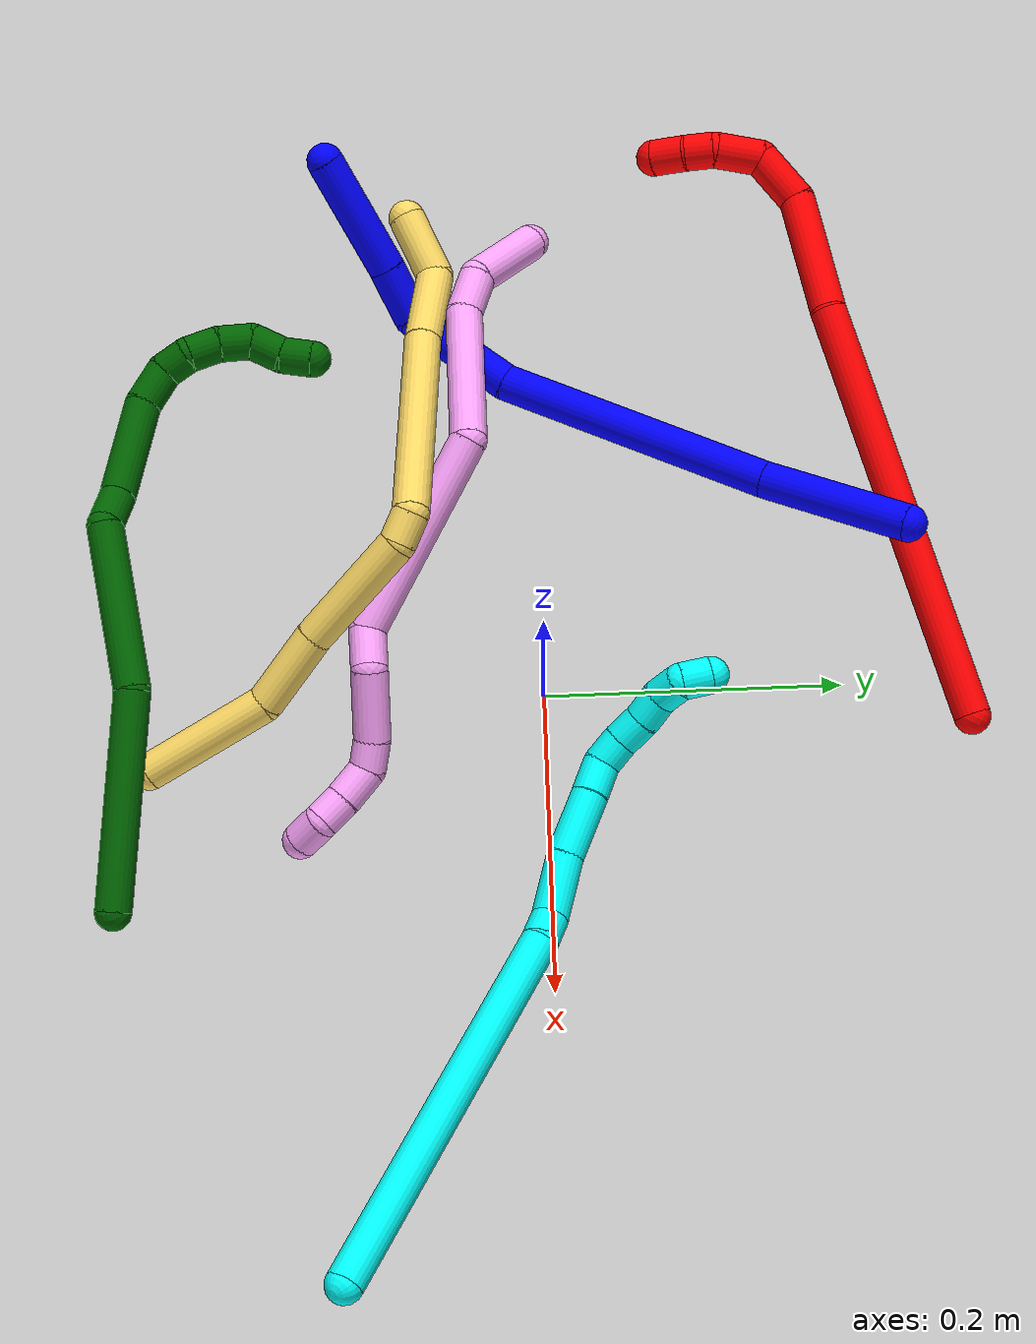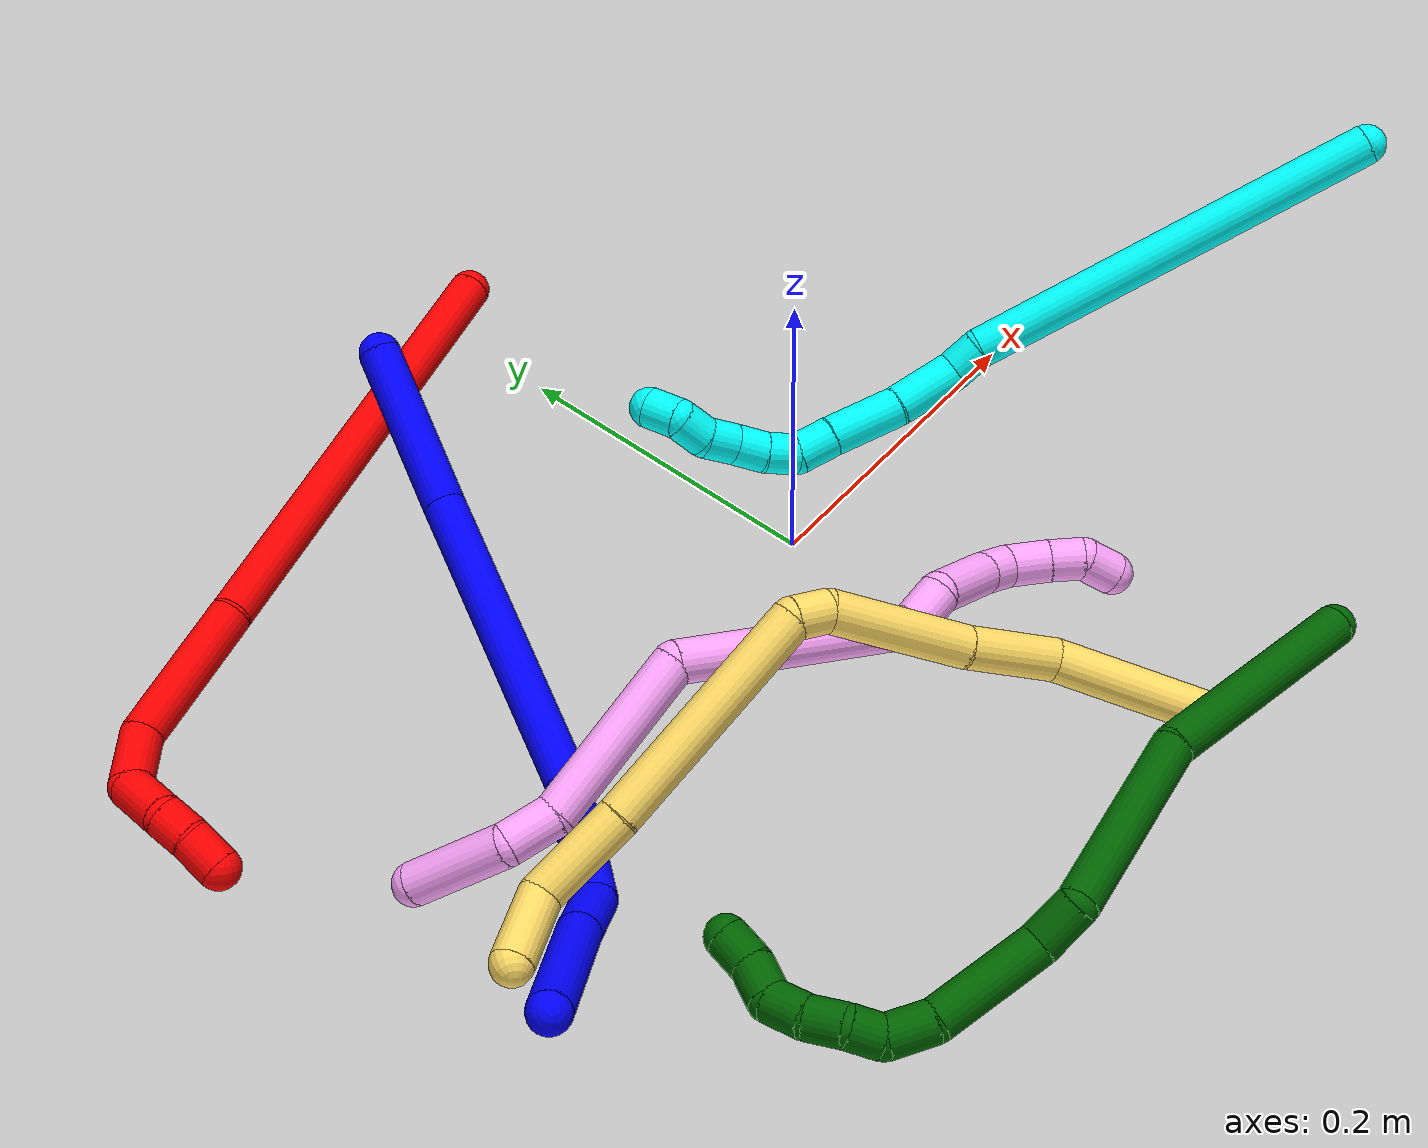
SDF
<sdf version="1.7">
 <world name="default">
  <plugin name="TubeGeneratorPlugin" filename="libtube_generator_plugin.so"/>
  <model name="photoneo_s_sensor">
   <static>1</static>
   <pose>0 0 2 1.57079 1.57079 3.14159</pose>
   <link name="link">
    <inertial><mass>0.1</mass></inertial>
    <sensor name="sensor" type="depth">
     <update_rate>30</update_rate>
     <camera>
      <horizontal_fov>1.22</horizontal_fov>
      <image><width>1920</width><height>1200</height><format>B8G8R8</format></image>
      <clip><near>0.1</near><far>4</far></clip>
      <depth_camera><output>points</output></depth_camera>
     </camera>
     <plugin name="camera_plugin" filename="libgazebo_ros_depth_camera.so">
      <baseline>0.2</baseline>
      <alwaysOn>1</alwaysOn>
      <updateRate>0.0</updateRate>
      <cameraName>camera_ir</cameraName>
      <imageTopicName>/camera/color/image_raw</imageTopicName>
      <cameraInfoTopicName>/camera/color/camera_info</cameraInfoTopicName>
      <depthImageTopicName>/camera/depth/image_raw</depthImageTopicName>
      <depthImageCameraInfoTopicName>/camera/depth/camera_info</depthImageCameraInfoTopicName>
      <pointCloudTopicName>/camera/depth/points</pointCloudTopicName>
      <frameName>fr_optical</frameName>
      <pointCloudCutoff>0.1</pointCloudCutoff>
      <pointCloudCutoffMax>2.0</pointCloudCutoffMax>
      <distortionK1>0</distortionK1>
      <distortionK2>0</distortionK2>
      <distortionK3>0</distortionK3>
      <distortionT1>0</distortionT1>
      <distortionT2>0</distortionT2>
      <CxPrime>0</CxPrime>
      <Cx>0</Cx>
      <Cy>0</Cy>
      <focalLength>0</focalLength>
      <hackBaseline>0</hackBaseline>
     </plugin>
    </sensor>
   </link>
  </model>
  <gravity>0 0 -9.8</gravity>
  <magnetic_field>6e-06 2.3e-05 -4.2e-05</magnetic_field>
  <atmosphere type="adiabatic"/>
  <physics name="default_physics" default="0" type="ode">
   <max_step_size>0.003</max_step_size>
   <real_time_factor>1</real_time_factor>
   <real_time_update_rate>1000</real_time_update_rate>
   <max_contacts>10000</max_contacts>
   <ode>
    <solver>
     <type>quick</type>
     <iters>100</iters>
     <sor>1.3</sor>
     <use_dynamic_moi_rescaling>0</use_dynamic_moi_rescaling>
    </solver>
    <constraints>
     <contact_max_correcting_vel>0</contact_max_correcting_vel>
     <contact_surface_layer>0.001</contact_surface_layer>
     <cfm>0</cfm>
     <erp>0.2</erp>
    </constraints>
   </ode>
  </physics>
  <scene><ambient>0.4 0.4 0.4 1</ambient><background>0.7 0.7 0.7 1</background><shadows>0</shadows></scene>
  <audio><device>default</device></audio>
  <spherical_coordinates>
   <surface_model>EARTH_WGS84</surface_model>
   <latitude_deg>0</latitude_deg>
   <longitude_deg>0</longitude_deg>
   <elevation>0</elevation>
   <heading_deg>0</heading_deg>
  </spherical_coordinates>
  <model name="bin">
   <static>1</static>
   <link name="bottom">
    <collision name="collision-bottom">
     <pose>0 0 -0.01 0 -0 0</pose>
     <geometry><box><size>0.8 0.6 0.02</size></box></geometry>
     <surface>
      <friction><ode><mu>100</mu><mu2>100</mu2></ode></friction>
      <contact><collide_bitmask>65535</collide_bitmask></contact>
     </surface>
    </collision>
   </link>
   <link name="west_wall">
    <collision name="collision-west_wall">
     <pose>-0.41 0 0.1 0 -0 0</pose>
     <geometry><box><size>0.02 0.6 0.2</size></box></geometry>
     <surface>
      <friction><ode><mu>100</mu><mu2>100</mu2></ode></friction>
      <contact><collide_bitmask>65535</collide_bitmask></contact>
     </surface>
    </collision>
   </link>
   <link name="east_wall">
    <collision name="collision-east_wall">
     <pose>0.41 0 0.1 0 -0 0</pose>
     <geometry><box><size>0.02 0.6 0.2</size></box></geometry>
     <surface>
      <friction><ode><mu>100</mu><mu2>100</mu2></ode></friction>
      <contact><collide_bitmask>65535</collide_bitmask></contact>
     </surface>
    </collision>
   </link>
   <link name="south_wall">
    <collision name="collision-south_wall">
     <pose>0 -0.31 0.1 0 -0 0</pose>
     <geometry><box><size>0.8 0.02 0.2</size></box></geometry>
     <surface>
      <friction><ode><mu>100</mu><mu2>100</mu2></ode></friction>
      <contact><collide_bitmask>65535</collide_bitmask></contact>
     </surface>
    </collision>
   </link>
   <link name="north_wall">
    <collision name="collision-north_wall">
     <pose>0 0.31 0.1 0 -0 0</pose>
     <geometry><box><size>0.8 0.02 0.2</size></box></geometry>
     <surface>
      <friction><ode><mu>100</mu><mu2>100</mu2></ode></friction>
      <contact><collide_bitmask>65535</collide_bitmask></contact>
     </surface>
    </collision>
   </link>
  </model>
  <model name="1">
   <static>0</static>
   <link name="1">
    <collision name="collision-cylinder-e_1_1_4">
     <pose>0.004265 -0.051858 -0.007072 1.70633 0.081313 0.093138</pose>
     <geometry><cylinder><radius>0.0125</radius><length>0.105022</length></cylinder></geometry>
     <surface>
      <friction><ode><mu>1.16</mu><mu2>1.16</mu2><slip1>0</slip1><slip2>0</slip2></ode></friction>
      <contact><ode><kp>1e+06</kp><kd>1</kd><max_vel>0</max_vel><min_depth>0.001</min_depth></ode></contact>
     </surface>
    </collision>
    <visual name="visual-cylinder-e_1_1_4">
     <pose>0.004265 -0.051858 -0.007072 1.70633 0.081313 0.093138</pose>
     <geometry><cylinder><radius>0.0125</radius><length>0.105022</length></cylinder></geometry>
     <material><ambient>0 0 1 1</ambient></material>
    </visual>
    <collision name="collision-cylinder-e_2_4_5">
     <pose>0.01842 -0.195874 -0.041775 1.86209 0.102433 0.137553</pose>
     <geometry><cylinder><radius>0.0125</radius><length>0.193438</length></cylinder></geometry>
     <surface>
      <friction><ode><mu>1.16</mu><mu2>1.16</mu2><slip1>0</slip1><slip2>0</slip2></ode></friction>
      <contact><ode><kp>1e+06</kp><kd>1</kd><max_vel>0</max_vel><min_depth>0.001</min_depth></ode></contact>
     </surface>
    </collision>
    <visual name="visual-cylinder-e_2_4_5">
     <pose>0.01842 -0.195874 -0.041775 1.86209 0.102433 0.137553</pose>
     <geometry><cylinder><radius>0.0125</radius><length>0.193438</length></cylinder></geometry>
     <material><ambient>0 0 1 1</ambient></material>
    </visual>
    <collision name="collision-cylinder-e_3_5_6">
     <pose>0.039805 -0.321623 -0.087193 2.05777 0.293686 0.481823</pose>
     <geometry><cylinder><radius>0.0125</radius><length>0.079417</length></cylinder></geometry>
     <surface>
      <friction><ode><mu>1.16</mu><mu2>1.16</mu2><slip1>0</slip1><slip2>0</slip2></ode></friction>
      <contact><ode><kp>1e+06</kp><kd>1</kd><max_vel>0</max_vel><min_depth>0.001</min_depth></ode></contact>
     </surface>
    </collision>
    <visual name="visual-cylinder-e_3_5_6">
     <pose>0.039805 -0.321623 -0.087193 2.05777 0.293686 0.481823</pose>
     <geometry><cylinder><radius>0.0125</radius><length>0.079417</length></cylinder></geometry>
     <material><ambient>0 0 1 1</ambient></material>
    </visual>
    <collision name="collision-cylinder-e_4_6_7">
     <pose>0.062319 -0.362114 -0.119208 2.69001 0.608543 1.87848</pose>
     <geometry><cylinder><radius>0.0125</radius><length>0.038549</length></cylinder></geometry>
     <surface>
      <friction><ode><mu>1.16</mu><mu2>1.16</mu2><slip1>0</slip1><slip2>0</slip2></ode></friction>
      <contact><ode><kp>1e+06</kp><kd>1</kd><max_vel>0</max_vel><min_depth>0.001</min_depth></ode></contact>
     </surface>
    </collision>
    <visual name="visual-cylinder-e_4_6_7">
     <pose>0.062319 -0.362114 -0.119208 2.69001 0.608543 1.87848</pose>
     <geometry><cylinder><radius>0.0125</radius><length>0.038549</length></cylinder></geometry>
     <material><ambient>0 0 1 1</ambient></material>
    </visual>
    <collision name="collision-cylinder-e_5_7_2">
     <pose>0.095687 -0.385654 -0.164579 2.65088 0.564326 1.71674</pose>
     <geometry><cylinder><radius>0.0125</radius><length>0.083574</length></cylinder></geometry>
     <surface>
      <friction><ode><mu>1.16</mu><mu2>1.16</mu2><slip1>0</slip1><slip2>0</slip2></ode></friction>
      <contact><ode><kp>1e+06</kp><kd>1</kd><max_vel>0</max_vel><min_depth>0.001</min_depth></ode></contact>
     </surface>
    </collision>
    <visual name="visual-cylinder-e_5_7_2">
     <pose>0.095687 -0.385654 -0.164579 2.65088 0.564326 1.71674</pose>
     <geometry><cylinder><radius>0.0125</radius><length>0.083574</length></cylinder></geometry>
     <material><ambient>0 0 1 1</ambient></material>
    </visual>
    <collision name="collision-sphere-2">
     <pose>0.118036 -0.402293 -0.19572 0 -0 0</pose>
     <geometry><sphere><radius>0.0125</radius></sphere></geometry>
     <surface>
      <friction><ode><mu>1.16</mu><mu2>1.16</mu2><slip1>0</slip1><slip2>0</slip2></ode></friction>
      <contact><ode><kp>1e+06</kp><kd>1</kd><max_vel>0</max_vel><min_depth>0.001</min_depth></ode></contact>
     </surface>
    </collision>
    <visual name="visual-sphere-2">
     <pose>0.118036 -0.402293 -0.19572 0 -0 0</pose>
     <geometry><sphere><radius>0.0125</radius></sphere></geometry>
     <material><ambient>0 0 1 1</ambient></material>
    </visual>
    <collision name="collision-sphere-7">
     <pose>0.073337 -0.369015 -0.133438 0 -0 0</pose>
     <geometry><sphere><radius>0.0125</radius></sphere></geometry>
     <surface>
      <friction><ode><mu>1.16</mu><mu2>1.16</mu2><slip1>0</slip1><slip2>0</slip2></ode></friction>
      <contact><ode><kp>1e+06</kp><kd>1</kd><max_vel>0</max_vel><min_depth>0.001</min_depth></ode></contact>
     </surface>
    </collision>
    <visual name="visual-sphere-7">
     <pose>0.073337 -0.369015 -0.133438 0 -0 0</pose>
     <geometry><sphere><radius>0.0125</radius></sphere></geometry>
     <material><ambient>0 0 1 1</ambient></material>
    </visual>
    <collision name="collision-sphere-6">
     <pose>0.0513 -0.355213 -0.104979 0 -0 0</pose>
     <geometry><sphere><radius>0.0125</radius></sphere></geometry>
     <surface>
      <friction><ode><mu>1.16</mu><mu2>1.16</mu2><slip1>0</slip1><slip2>0</slip2></ode></friction>
      <contact><ode><kp>1e+06</kp><kd>1</kd><max_vel>0</max_vel><min_depth>0.001</min_depth></ode></contact>
     </surface>
    </collision>
    <visual name="visual-sphere-6">
     <pose>0.0513 -0.355213 -0.104979 0 -0 0</pose>
     <geometry><sphere><radius>0.0125</radius></sphere></geometry>
     <material><ambient>0 0 1 1</ambient></material>
    </visual>
    <collision name="collision-sphere-5">
     <pose>0.02831 -0.288033 -0.069407 0 -0 0</pose>
     <geometry><sphere><radius>0.0125</radius></sphere></geometry>
     <surface>
      <friction><ode><mu>1.16</mu><mu2>1.16</mu2><slip1>0</slip1><slip2>0</slip2></ode></friction>
      <contact><ode><kp>1e+06</kp><kd>1</kd><max_vel>0</max_vel><min_depth>0.001</min_depth></ode></contact>
     </surface>
    </collision>
    <visual name="visual-sphere-5">
     <pose>0.02831 -0.288033 -0.069407 0 -0 0</pose>
     <geometry><sphere><radius>0.0125</radius></sphere></geometry>
     <material><ambient>0 0 1 1</ambient></material>
    </visual>
    <collision name="collision-sphere-1">
     <geometry><sphere><radius>0.0125</radius></sphere></geometry>
     <surface>
      <friction><ode><mu>1.16</mu><mu2>1.16</mu2><slip1>0</slip1><slip2>0</slip2></ode></friction>
      <contact><ode><kp>1e+06</kp><kd>1</kd><max_vel>0</max_vel><min_depth>0.001</min_depth></ode></contact>
     </surface>
    </collision>
    <visual name="visual-sphere-1">
     <geometry><sphere><radius>0.0125</radius></sphere></geometry>
     <material><ambient>0 0 1 1</ambient></material>
    </visual>
    <collision name="collision-sphere-4">
     <pose>0.00853 -0.103715 -0.014144 0 -0 0</pose>
     <geometry><sphere><radius>0.0125</radius></sphere></geometry>
     <surface>
      <friction><ode><mu>1.16</mu><mu2>1.16</mu2><slip1>0</slip1><slip2>0</slip2></ode></friction>
      <contact><ode><kp>1e+06</kp><kd>1</kd><max_vel>0</max_vel><min_depth>0.001</min_depth></ode></contact>
     </surface>
    </collision>
    <visual name="visual-sphere-4">
     <pose>0.00853 -0.103715 -0.014144 0 -0 0</pose>
     <geometry><sphere><radius>0.0125</radius></sphere></geometry>
     <material><ambient>0 0 1 1</ambient></material>
    </visual>
    <inertial>
     <pose>0.035143 -0.230135 -0.068196 0 -0 0</pose>
     <mass>0.5</mass>
     <inertia>
      <ixx>0.000902</ixx>
      <ixy>0</ixy>
      <ixz>0</ixz>
      <iyy>-3.9e-05</iyy>
      <iyz>0</iyz>
      <izz>0.000612</izz>
     </inertia>
    </inertial>
   </link>
   <pose>-0.089279 0.242861 0.076738 2.68162 -0.008813 2.77817</pose>
  </model>
  <model name="2">
   <static>0</static>
   <link name="2">
    <collision name="collision-cylinder-e_1_1_4">
     <pose>-0.04969 -0.092992 0.103955 0.729788 -0.342239 -0.131835</pose>
     <geometry><cylinder><radius>0.0125</radius><length>0.296131</length></cylinder></geometry>
     <surface>
      <friction><ode><mu>1.16</mu><mu2>1.16</mu2><slip1>0</slip1><slip2>0</slip2></ode></friction>
      <contact><ode><kp>1e+06</kp><kd>1</kd><max_vel>0</max_vel><min_depth>0.001</min_depth></ode></contact>
     </surface>
    </collision>
    <visual name="visual-cylinder-e_1_1_4">
     <pose>-0.04969 -0.092992 0.103955 0.729788 -0.342239 -0.131835</pose>
     <geometry><cylinder><radius>0.0125</radius><length>0.296131</length></cylinder></geometry>
     <material><ambient>1 0 0 1</ambient></material>
    </visual>
    <collision name="collision-cylinder-e_2_4_5">
     <pose>-0.120975 -0.208218 0.239619 0.611547 -0.50867 -0.163761</pose>
     <geometry><cylinder><radius>0.0125</radius><length>0.088682</length></cylinder></geometry>
     <surface>
      <friction><ode><mu>1.16</mu><mu2>1.16</mu2><slip1>0</slip1><slip2>0</slip2></ode></friction>
      <contact><ode><kp>1e+06</kp><kd>1</kd><max_vel>0</max_vel><min_depth>0.001</min_depth></ode></contact>
     </surface>
    </collision>
    <visual name="visual-cylinder-e_2_4_5">
     <pose>-0.120975 -0.208218 0.239619 0.611547 -0.50867 -0.163761</pose>
     <geometry><cylinder><radius>0.0125</radius><length>0.088682</length></cylinder></geometry>
     <material><ambient>1 0 0 1</ambient></material>
    </visual>
    <collision name="collision-cylinder-e_3_5_6">
     <pose>-0.147418 -0.247608 0.279114 1.14472 -0.25187 -0.162784</pose>
     <geometry><cylinder><radius>0.0125</radius><length>0.038906</length></cylinder></geometry>
     <surface>
      <friction><ode><mu>1.16</mu><mu2>1.16</mu2><slip1>0</slip1><slip2>0</slip2></ode></friction>
      <contact><ode><kp>1e+06</kp><kd>1</kd><max_vel>0</max_vel><min_depth>0.001</min_depth></ode></contact>
     </surface>
    </collision>
    <visual name="visual-cylinder-e_3_5_6">
     <pose>-0.147418 -0.247608 0.279114 1.14472 -0.25187 -0.162784</pose>
     <geometry><cylinder><radius>0.0125</radius><length>0.038906</length></cylinder></geometry>
     <material><ambient>1 0 0 1</ambient></material>
    </visual>
    <collision name="collision-cylinder-e_4_6_7">
     <pose>-0.152096 -0.280642 0.282109 1.86379 0.010244 0.013791</pose>
     <geometry><cylinder><radius>0.0125</radius><length>0.033174</length></cylinder></geometry>
     <surface>
      <friction><ode><mu>1.16</mu><mu2>1.16</mu2><slip1>0</slip1><slip2>0</slip2></ode></friction>
      <contact><ode><kp>1e+06</kp><kd>1</kd><max_vel>0</max_vel><min_depth>0.001</min_depth></ode></contact>
     </surface>
    </collision>
    <visual name="visual-cylinder-e_4_6_7">
     <pose>-0.152096 -0.280642 0.282109 1.86379 0.010244 0.013791</pose>
     <geometry><cylinder><radius>0.0125</radius><length>0.033174</length></cylinder></geometry>
     <material><ambient>1 0 0 1</ambient></material>
    </visual>
    <collision name="collision-cylinder-e_5_7_8">
     <pose>-0.154829 -0.304668 0.272221 2.12994 -0.293398 -0.521392</pose>
     <geometry><cylinder><radius>0.0125</radius><length>0.020078</length></cylinder></geometry>
     <surface>
      <friction><ode><mu>1.16</mu><mu2>1.16</mu2><slip1>0</slip1><slip2>0</slip2></ode></friction>
      <contact><ode><kp>1e+06</kp><kd>1</kd><max_vel>0</max_vel><min_depth>0.001</min_depth></ode></contact>
     </surface>
    </collision>
    <visual name="visual-cylinder-e_5_7_8">
     <pose>-0.154829 -0.304668 0.272221 2.12994 -0.293398 -0.521392</pose>
     <geometry><cylinder><radius>0.0125</radius><length>0.020078</length></cylinder></geometry>
     <material><ambient>1 0 0 1</ambient></material>
    </visual>
    <collision name="collision-cylinder-e_6_8_2">
     <pose>-0.162967 -0.321288 0.261345 2.16937 -0.471896 -0.854019</pose>
     <geometry><cylinder><radius>0.0125</radius><length>0.023029</length></cylinder></geometry>
     <surface>
      <friction><ode><mu>1.16</mu><mu2>1.16</mu2><slip1>0</slip1><slip2>0</slip2></ode></friction>
      <contact><ode><kp>1e+06</kp><kd>1</kd><max_vel>0</max_vel><min_depth>0.001</min_depth></ode></contact>
     </surface>
    </collision>
    <visual name="visual-cylinder-e_6_8_2">
     <pose>-0.162967 -0.321288 0.261345 2.16937 -0.471896 -0.854019</pose>
     <geometry><cylinder><radius>0.0125</radius><length>0.023029</length></cylinder></geometry>
     <material><ambient>1 0 0 1</ambient></material>
    </visual>
    <collision name="collision-sphere-2">
     <pose>-0.168201 -0.329761 0.255566 0 -0 0</pose>
     <geometry><sphere><radius>0.0125</radius></sphere></geometry>
     <surface>
      <friction><ode><mu>1.16</mu><mu2>1.16</mu2><slip1>0</slip1><slip2>0</slip2></ode></friction>
      <contact><ode><kp>1e+06</kp><kd>1</kd><max_vel>0</max_vel><min_depth>0.001</min_depth></ode></contact>
     </surface>
    </collision>
    <visual name="visual-sphere-2">
     <pose>-0.168201 -0.329761 0.255566 0 -0 0</pose>
     <geometry><sphere><radius>0.0125</radius></sphere></geometry>
     <material><ambient>1 0 0 1</ambient></material>
    </visual>
    <collision name="collision-sphere-4">
     <pose>-0.099381 -0.185984 0.207911 0 -0 0</pose>
     <geometry><sphere><radius>0.0125</radius></sphere></geometry>
     <surface>
      <friction><ode><mu>1.16</mu><mu2>1.16</mu2><slip1>0</slip1><slip2>0</slip2></ode></friction>
      <contact><ode><kp>1e+06</kp><kd>1</kd><max_vel>0</max_vel><min_depth>0.001</min_depth></ode></contact>
     </surface>
    </collision>
    <visual name="visual-sphere-4">
     <pose>-0.099381 -0.185984 0.207911 0 -0 0</pose>
     <geometry><sphere><radius>0.0125</radius></sphere></geometry>
     <material><ambient>1 0 0 1</ambient></material>
    </visual>
    <collision name="collision-sphere-1">
     <geometry><sphere><radius>0.0125</radius></sphere></geometry>
     <surface>
      <friction><ode><mu>1.16</mu><mu2>1.16</mu2><slip1>0</slip1><slip2>0</slip2></ode></friction>
      <contact><ode><kp>1e+06</kp><kd>1</kd><max_vel>0</max_vel><min_depth>0.001</min_depth></ode></contact>
     </surface>
    </collision>
    <visual name="visual-sphere-1">
     <geometry><sphere><radius>0.0125</radius></sphere></geometry>
     <material><ambient>1 0 0 1</ambient></material>
    </visual>
    <collision name="collision-sphere-8">
     <pose>-0.157733 -0.312815 0.267124 0 -0 0</pose>
     <geometry><sphere><radius>0.0125</radius></sphere></geometry>
     <surface>
      <friction><ode><mu>1.16</mu><mu2>1.16</mu2><slip1>0</slip1><slip2>0</slip2></ode></friction>
      <contact><ode><kp>1e+06</kp><kd>1</kd><max_vel>0</max_vel><min_depth>0.001</min_depth></ode></contact>
     </surface>
    </collision>
    <visual name="visual-sphere-8">
     <pose>-0.157733 -0.312815 0.267124 0 -0 0</pose>
     <geometry><sphere><radius>0.0125</radius></sphere></geometry>
     <material><ambient>1 0 0 1</ambient></material>
    </visual>
    <collision name="collision-sphere-5">
     <pose>-0.14257 -0.230453 0.271327 0 -0 0</pose>
     <geometry><sphere><radius>0.0125</radius></sphere></geometry>
     <surface>
      <friction><ode><mu>1.16</mu><mu2>1.16</mu2><slip1>0</slip1><slip2>0</slip2></ode></friction>
      <contact><ode><kp>1e+06</kp><kd>1</kd><max_vel>0</max_vel><min_depth>0.001</min_depth></ode></contact>
     </surface>
    </collision>
    <visual name="visual-sphere-5">
     <pose>-0.14257 -0.230453 0.271327 0 -0 0</pose>
     <geometry><sphere><radius>0.0125</radius></sphere></geometry>
     <material><ambient>1 0 0 1</ambient></material>
    </visual>
    <collision name="collision-sphere-6">
     <pose>-0.152266 -0.264763 0.2869 0 -0 0</pose>
     <geometry><sphere><radius>0.0125</radius></sphere></geometry>
     <surface>
      <friction><ode><mu>1.16</mu><mu2>1.16</mu2><slip1>0</slip1><slip2>0</slip2></ode></friction>
      <contact><ode><kp>1e+06</kp><kd>1</kd><max_vel>0</max_vel><min_depth>0.001</min_depth></ode></contact>
     </surface>
    </collision>
    <visual name="visual-sphere-6">
     <pose>-0.152266 -0.264763 0.2869 0 -0 0</pose>
     <geometry><sphere><radius>0.0125</radius></sphere></geometry>
     <material><ambient>1 0 0 1</ambient></material>
    </visual>
    <collision name="collision-sphere-7">
     <pose>-0.151926 -0.296522 0.277319 0 -0 0</pose>
     <geometry><sphere><radius>0.0125</radius></sphere></geometry>
     <surface>
      <friction><ode><mu>1.16</mu><mu2>1.16</mu2><slip1>0</slip1><slip2>0</slip2></ode></friction>
      <contact><ode><kp>1e+06</kp><kd>1</kd><max_vel>0</max_vel><min_depth>0.001</min_depth></ode></contact>
     </surface>
    </collision>
    <visual name="visual-sphere-7">
     <pose>-0.151926 -0.296522 0.277319 0 -0 0</pose>
     <geometry><sphere><radius>0.0125</radius></sphere></geometry>
     <material><ambient>1 0 0 1</ambient></material>
    </visual>
    <inertial>
     <pose>-0.086172 -0.156925 0.167473 0 -0 0</pose>
     <mass>0.5</mass>
     <inertia>
      <ixx>0.001803</ixx>
      <ixy>0</ixy>
      <ixz>0</ixz>
      <iyy>0.001418</iyy>
      <iyz>0</iyz>
      <izz>0.002193</izz>
     </inertia>
    </inertial>
   </link>
   <pose>0.027063 0.28527 0.011498 -0.843025 -1.18651 0.380143</pose>
  </model>
  <model name="3">
   <static>0</static>
   <link name="3">
    <collision name="collision-cylinder-e_1_1_4">
     <pose>-0.052923 -0.005029 -0.121755 3.10031 -0.40972 -2.94355</pose>
     <geometry><cylinder><radius>0.0125</radius><length>0.265709</length></cylinder></geometry>
     <surface>
      <friction><ode><mu>1.16</mu><mu2>1.16</mu2><slip1>0</slip1><slip2>0</slip2></ode></friction>
      <contact><ode><kp>1e+06</kp><kd>1</kd><max_vel>0</max_vel><min_depth>0.001</min_depth></ode></contact>
     </surface>
    </collision>
    <visual name="visual-cylinder-e_1_1_4">
     <pose>-0.052923 -0.005029 -0.121755 3.10031 -0.40972 -2.94355</pose>
     <geometry><cylinder><radius>0.0125</radius><length>0.265709</length></cylinder></geometry>
     <material><ambient>0.003922 1 0.996078 1</ambient></material>
    </visual>
    <collision name="collision-cylinder-e_2_4_5">
     <pose>-0.108329 -0.012641 -0.253765 2.89482 -0.230607 -1.50244</pose>
     <geometry><cylinder><radius>0.0125</radius><length>0.021727</length></cylinder></geometry>
     <surface>
      <friction><ode><mu>1.16</mu><mu2>1.16</mu2><slip1>0</slip1><slip2>0</slip2></ode></friction>
      <contact><ode><kp>1e+06</kp><kd>1</kd><max_vel>0</max_vel><min_depth>0.001</min_depth></ode></contact>
     </surface>
    </collision>
    <visual name="visual-cylinder-e_2_4_5">
     <pose>-0.108329 -0.012641 -0.253765 2.89482 -0.230607 -1.50244</pose>
     <geometry><cylinder><radius>0.0125</radius><length>0.021727</length></cylinder></geometry>
     <material><ambient>0.003922 1 0.996078 1</ambient></material>
    </visual>
    <collision name="collision-cylinder-e_3_5_6">
     <pose>-0.124841 -0.018712 -0.280149 2.92861 -0.704593 -2.57565</pose>
     <geometry><cylinder><radius>0.0125</radius><length>0.043318</length></cylinder></geometry>
     <surface>
      <friction><ode><mu>1.16</mu><mu2>1.16</mu2><slip1>0</slip1><slip2>0</slip2></ode></friction>
      <contact><ode><kp>1e+06</kp><kd>1</kd><max_vel>0</max_vel><min_depth>0.001</min_depth></ode></contact>
     </surface>
    </collision>
    <visual name="visual-cylinder-e_3_5_6">
     <pose>-0.124841 -0.018712 -0.280149 2.92861 -0.704593 -2.57565</pose>
     <geometry><cylinder><radius>0.0125</radius><length>0.043318</length></cylinder></geometry>
     <material><ambient>0.003922 1 0.996078 1</ambient></material>
    </visual>
    <collision name="collision-cylinder-e_4_6_7">
     <pose>-0.152989 -0.022893 -0.314025 3.10257 -0.67164 -3.02991</pose>
     <geometry><cylinder><radius>0.0125</radius><length>0.045379</length></cylinder></geometry>
     <surface>
      <friction><ode><mu>1.16</mu><mu2>1.16</mu2><slip1>0</slip1><slip2>0</slip2></ode></friction>
      <contact><ode><kp>1e+06</kp><kd>1</kd><max_vel>0</max_vel><min_depth>0.001</min_depth></ode></contact>
     </surface>
    </collision>
    <visual name="visual-cylinder-e_4_6_7">
     <pose>-0.152989 -0.022893 -0.314025 3.10257 -0.67164 -3.02991</pose>
     <geometry><cylinder><radius>0.0125</radius><length>0.045379</length></cylinder></geometry>
     <material><ambient>0.003922 1 0.996078 1</ambient></material>
    </visual>
    <collision name="collision-cylinder-e_5_7_8">
     <pose>-0.174168 -0.024471 -0.34123 3.04828 -0.63921 -2.8613</pose>
     <geometry><cylinder><radius>0.0125</radius><length>0.023671</length></cylinder></geometry>
     <surface>
      <friction><ode><mu>1.16</mu><mu2>1.16</mu2><slip1>0</slip1><slip2>0</slip2></ode></friction>
      <contact><ode><kp>1e+06</kp><kd>1</kd><max_vel>0</max_vel><min_depth>0.001</min_depth></ode></contact>
     </surface>
    </collision>
    <visual name="visual-cylinder-e_5_7_8">
     <pose>-0.174168 -0.024471 -0.34123 3.04828 -0.63921 -2.8613</pose>
     <geometry><cylinder><radius>0.0125</radius><length>0.023671</length></cylinder></geometry>
     <material><ambient>0.003922 1 0.996078 1</ambient></material>
    </visual>
    <collision name="collision-cylinder-e_6_8_9">
     <pose>-0.187984 -0.021308 -0.35691 -2.56477 -0.738259 1.83314</pose>
     <geometry><cylinder><radius>0.0125</radius><length>0.020073</length></cylinder></geometry>
     <surface>
      <friction><ode><mu>1.16</mu><mu2>1.16</mu2><slip1>0</slip1><slip2>0</slip2></ode></friction>
      <contact><ode><kp>1e+06</kp><kd>1</kd><max_vel>0</max_vel><min_depth>0.001</min_depth></ode></contact>
     </surface>
    </collision>
    <visual name="visual-cylinder-e_6_8_9">
     <pose>-0.187984 -0.021308 -0.35691 -2.56477 -0.738259 1.83314</pose>
     <geometry><cylinder><radius>0.0125</radius><length>0.020073</length></cylinder></geometry>
     <material><ambient>0.003922 1 0.996078 1</ambient></material>
    </visual>
    <collision name="collision-cylinder-e_7_9_10">
     <pose>-0.201326 -0.011598 -0.368152 -2.29618 -0.716425 1.38819</pose>
     <geometry><cylinder><radius>0.0125</radius><length>0.020064</length></cylinder></geometry>
     <surface>
      <friction><ode><mu>1.16</mu><mu2>1.16</mu2><slip1>0</slip1><slip2>0</slip2></ode></friction>
      <contact><ode><kp>1e+06</kp><kd>1</kd><max_vel>0</max_vel><min_depth>0.001</min_depth></ode></contact>
     </surface>
    </collision>
    <visual name="visual-cylinder-e_7_9_10">
     <pose>-0.201326 -0.011598 -0.368152 -2.29618 -0.716425 1.38819</pose>
     <geometry><cylinder><radius>0.0125</radius><length>0.020064</length></cylinder></geometry>
     <material><ambient>0.003922 1 0.996078 1</ambient></material>
    </visual>
    <collision name="collision-cylinder-e_8_10_11">
     <pose>-0.215701 -0.001235 -0.377337 -2.29584 -0.891944 1.63126</pose>
     <geometry><cylinder><radius>0.0125</radius><length>0.020011</length></cylinder></geometry>
     <surface>
      <friction><ode><mu>1.16</mu><mu2>1.16</mu2><slip1>0</slip1><slip2>0</slip2></ode></friction>
      <contact><ode><kp>1e+06</kp><kd>1</kd><max_vel>0</max_vel><min_depth>0.001</min_depth></ode></contact>
     </surface>
    </collision>
    <visual name="visual-cylinder-e_8_10_11">
     <pose>-0.215701 -0.001235 -0.377337 -2.29584 -0.891944 1.63126</pose>
     <geometry><cylinder><radius>0.0125</radius><length>0.020011</length></cylinder></geometry>
     <material><ambient>0.003922 1 0.996078 1</ambient></material>
    </visual>
    <collision name="collision-cylinder-e_9_11_12">
     <pose>-0.230087 0.010786 -0.383252 -1.80536 -0.71989 0.889943</pose>
     <geometry><cylinder><radius>0.0125</radius><length>0.020016</length></cylinder></geometry>
     <surface>
      <friction><ode><mu>1.16</mu><mu2>1.16</mu2><slip1>0</slip1><slip2>0</slip2></ode></friction>
      <contact><ode><kp>1e+06</kp><kd>1</kd><max_vel>0</max_vel><min_depth>0.001</min_depth></ode></contact>
     </surface>
    </collision>
    <visual name="visual-cylinder-e_9_11_12">
     <pose>-0.230087 0.010786 -0.383252 -1.80536 -0.71989 0.889943</pose>
     <geometry><cylinder><radius>0.0125</radius><length>0.020016</length></cylinder></geometry>
     <material><ambient>0.003922 1 0.996078 1</ambient></material>
    </visual>
    <collision name="collision-cylinder-e_10_12_2">
     <pose>-0.237624 0.025431 -0.391767 -2.3165 -0.093848 0.213768</pose>
     <geometry><cylinder><radius>0.0125</radius><length>0.020033</length></cylinder></geometry>
     <surface>
      <friction><ode><mu>1.16</mu><mu2>1.16</mu2><slip1>0</slip1><slip2>0</slip2></ode></friction>
      <contact><ode><kp>1e+06</kp><kd>1</kd><max_vel>0</max_vel><min_depth>0.001</min_depth></ode></contact>
     </surface>
    </collision>
    <visual name="visual-cylinder-e_10_12_2">
     <pose>-0.237624 0.025431 -0.391767 -2.3165 -0.093848 0.213768</pose>
     <geometry><cylinder><radius>0.0125</radius><length>0.020033</length></cylinder></geometry>
     <material><ambient>0.003922 1 0.996078 1</ambient></material>
    </visual>
    <collision name="collision-sphere-2">
     <pose>-0.238562 0.032756 -0.398533 0 -0 0</pose>
     <geometry><sphere><radius>0.0125</radius></sphere></geometry>
     <surface>
      <friction><ode><mu>1.16</mu><mu2>1.16</mu2><slip1>0</slip1><slip2>0</slip2></ode></friction>
      <contact><ode><kp>1e+06</kp><kd>1</kd><max_vel>0</max_vel><min_depth>0.001</min_depth></ode></contact>
     </surface>
    </collision>
    <visual name="visual-sphere-2">
     <pose>-0.238562 0.032756 -0.398533 0 -0 0</pose>
     <geometry><sphere><radius>0.0125</radius></sphere></geometry>
     <material><ambient>0.003922 1 0.996078 1</ambient></material>
    </visual>
    <collision name="collision-sphere-12">
     <pose>-0.236685 0.018105 -0.385001 0 -0 0</pose>
     <geometry><sphere><radius>0.0125</radius></sphere></geometry>
     <surface>
      <friction><ode><mu>1.16</mu><mu2>1.16</mu2><slip1>0</slip1><slip2>0</slip2></ode></friction>
      <contact><ode><kp>1e+06</kp><kd>1</kd><max_vel>0</max_vel><min_depth>0.001</min_depth></ode></contact>
     </surface>
    </collision>
    <visual name="visual-sphere-12">
     <pose>-0.236685 0.018105 -0.385001 0 -0 0</pose>
     <geometry><sphere><radius>0.0125</radius></sphere></geometry>
     <material><ambient>0.003922 1 0.996078 1</ambient></material>
    </visual>
    <collision name="collision-sphere-11">
     <pose>-0.223488 0.003467 -0.381503 0 -0 0</pose>
     <geometry><sphere><radius>0.0125</radius></sphere></geometry>
     <surface>
      <friction><ode><mu>1.16</mu><mu2>1.16</mu2><slip1>0</slip1><slip2>0</slip2></ode></friction>
      <contact><ode><kp>1e+06</kp><kd>1</kd><max_vel>0</max_vel><min_depth>0.001</min_depth></ode></contact>
     </surface>
    </collision>
    <visual name="visual-sphere-11">
     <pose>-0.223488 0.003467 -0.381503 0 -0 0</pose>
     <geometry><sphere><radius>0.0125</radius></sphere></geometry>
     <material><ambient>0.003922 1 0.996078 1</ambient></material>
    </visual>
    <collision name="collision-sphere-10">
     <pose>-0.207914 -0.005937 -0.373171 0 -0 0</pose>
     <geometry><sphere><radius>0.0125</radius></sphere></geometry>
     <surface>
      <friction><ode><mu>1.16</mu><mu2>1.16</mu2><slip1>0</slip1><slip2>0</slip2></ode></friction>
      <contact><ode><kp>1e+06</kp><kd>1</kd><max_vel>0</max_vel><min_depth>0.001</min_depth></ode></contact>
     </surface>
    </collision>
    <visual name="visual-sphere-10">
     <pose>-0.207914 -0.005937 -0.373171 0 -0 0</pose>
     <geometry><sphere><radius>0.0125</radius></sphere></geometry>
     <material><ambient>0.003922 1 0.996078 1</ambient></material>
    </visual>
    <collision name="collision-sphere-9">
     <pose>-0.194738 -0.017259 -0.363132 0 -0 0</pose>
     <geometry><sphere><radius>0.0125</radius></sphere></geometry>
     <surface>
      <friction><ode><mu>1.16</mu><mu2>1.16</mu2><slip1>0</slip1><slip2>0</slip2></ode></friction>
      <contact><ode><kp>1e+06</kp><kd>1</kd><max_vel>0</max_vel><min_depth>0.001</min_depth></ode></contact>
     </surface>
    </collision>
    <visual name="visual-sphere-9">
     <pose>-0.194738 -0.017259 -0.363132 0 -0 0</pose>
     <geometry><sphere><radius>0.0125</radius></sphere></geometry>
     <material><ambient>0.003922 1 0.996078 1</ambient></material>
    </visual>
    <collision name="collision-sphere-4">
     <pose>-0.105846 -0.010057 -0.243509 0 -0 0</pose>
     <geometry><sphere><radius>0.0125</radius></sphere></geometry>
     <surface>
      <friction><ode><mu>1.16</mu><mu2>1.16</mu2><slip1>0</slip1><slip2>0</slip2></ode></friction>
      <contact><ode><kp>1e+06</kp><kd>1</kd><max_vel>0</max_vel><min_depth>0.001</min_depth></ode></contact>
     </surface>
    </collision>
    <visual name="visual-sphere-4">
     <pose>-0.105846 -0.010057 -0.243509 0 -0 0</pose>
     <geometry><sphere><radius>0.0125</radius></sphere></geometry>
     <material><ambient>0.003922 1 0.996078 1</ambient></material>
    </visual>
    <collision name="collision-sphere-1">
     <geometry><sphere><radius>0.0125</radius></sphere></geometry>
     <surface>
      <friction><ode><mu>1.16</mu><mu2>1.16</mu2><slip1>0</slip1><slip2>0</slip2></ode></friction>
      <contact><ode><kp>1e+06</kp><kd>1</kd><max_vel>0</max_vel><min_depth>0.001</min_depth></ode></contact>
     </surface>
    </collision>
    <visual name="visual-sphere-1">
     <geometry><sphere><radius>0.0125</radius></sphere></geometry>
     <material><ambient>0.003922 1 0.996078 1</ambient></material>
    </visual>
    <collision name="collision-sphere-8">
     <pose>-0.181229 -0.025356 -0.350688 0 -0 0</pose>
     <geometry><sphere><radius>0.0125</radius></sphere></geometry>
     <surface>
      <friction><ode><mu>1.16</mu><mu2>1.16</mu2><slip1>0</slip1><slip2>0</slip2></ode></friction>
      <contact><ode><kp>1e+06</kp><kd>1</kd><max_vel>0</max_vel><min_depth>0.001</min_depth></ode></contact>
     </surface>
    </collision>
    <visual name="visual-sphere-8">
     <pose>-0.181229 -0.025356 -0.350688 0 -0 0</pose>
     <geometry><sphere><radius>0.0125</radius></sphere></geometry>
     <material><ambient>0.003922 1 0.996078 1</ambient></material>
    </visual>
    <collision name="collision-sphere-5">
     <pose>-0.110812 -0.015224 -0.26402 0 -0 0</pose>
     <geometry><sphere><radius>0.0125</radius></sphere></geometry>
     <surface>
      <friction><ode><mu>1.16</mu><mu2>1.16</mu2><slip1>0</slip1><slip2>0</slip2></ode></friction>
      <contact><ode><kp>1e+06</kp><kd>1</kd><max_vel>0</max_vel><min_depth>0.001</min_depth></ode></contact>
     </surface>
    </collision>
    <visual name="visual-sphere-5">
     <pose>-0.110812 -0.015224 -0.26402 0 -0 0</pose>
     <geometry><sphere><radius>0.0125</radius></sphere></geometry>
     <material><ambient>0.003922 1 0.996078 1</ambient></material>
    </visual>
    <collision name="collision-sphere-6">
     <pose>-0.13887 -0.0222 -0.296277 0 -0 0</pose>
     <geometry><sphere><radius>0.0125</radius></sphere></geometry>
     <surface>
      <friction><ode><mu>1.16</mu><mu2>1.16</mu2><slip1>0</slip1><slip2>0</slip2></ode></friction>
      <contact><ode><kp>1e+06</kp><kd>1</kd><max_vel>0</max_vel><min_depth>0.001</min_depth></ode></contact>
     </surface>
    </collision>
    <visual name="visual-sphere-6">
     <pose>-0.13887 -0.0222 -0.296277 0 -0 0</pose>
     <geometry><sphere><radius>0.0125</radius></sphere></geometry>
     <material><ambient>0.003922 1 0.996078 1</ambient></material>
    </visual>
    <collision name="collision-sphere-7">
     <pose>-0.167108 -0.023586 -0.331773 0 -0 0</pose>
     <geometry><sphere><radius>0.0125</radius></sphere></geometry>
     <surface>
      <friction><ode><mu>1.16</mu><mu2>1.16</mu2><slip1>0</slip1><slip2>0</slip2></ode></friction>
      <contact><ode><kp>1e+06</kp><kd>1</kd><max_vel>0</max_vel><min_depth>0.001</min_depth></ode></contact>
     </surface>
    </collision>
    <visual name="visual-sphere-7">
     <pose>-0.167108 -0.023586 -0.331773 0 -0 0</pose>
     <geometry><sphere><radius>0.0125</radius></sphere></geometry>
     <material><ambient>0.003922 1 0.996078 1</ambient></material>
    </visual>
    <inertial>
     <pose>-0.108767 -0.007999 -0.219897 0 -0 0</pose>
     <mass>0.5</mass>
     <inertia>
      <ixx>-0.001732</ixx>
      <ixy>0</ixy>
      <ixz>0</ixz>
      <iyy>0.001284</iyy>
      <iyz>0</iyz>
      <izz>0.00067</izz>
     </inertia>
    </inertial>
   </link>
   <pose>0.387923 -0.135842 0.123117 0.62655 0.700864 0.037633</pose>
  </model>
  <model name="4">
   <static>0</static>
   <link name="4">
    <collision name="collision-cylinder-e_1_1_4">
     <pose>0.01858 -0.023678 -0.002997 1.69669 0.661492 0.74294</pose>
     <geometry><cylinder><radius>0.0125</radius><length>0.060493</length></cylinder></geometry>
     <surface>
      <friction><ode><mu>1.16</mu><mu2>1.16</mu2><slip1>0</slip1><slip2>0</slip2></ode></friction>
      <contact><ode><kp>1e+06</kp><kd>1</kd><max_vel>0</max_vel><min_depth>0.001</min_depth></ode></contact>
     </surface>
    </collision>
    <visual name="visual-cylinder-e_1_1_4">
     <pose>0.01858 -0.023678 -0.002997 1.69669 0.661492 0.74294</pose>
     <geometry><cylinder><radius>0.0125</radius><length>0.060493</length></cylinder></geometry>
     <material><ambient>1 0.65098 0.996078 1</ambient></material>
    </visual>
    <collision name="collision-cylinder-e_2_4_5">
     <pose>0.048871 -0.055034 -0.000437 0.944297 0.890377 0.478004</pose>
     <geometry><cylinder><radius>0.0125</radius><length>0.030131</length></cylinder></geometry>
     <surface>
      <friction><ode><mu>1.16</mu><mu2>1.16</mu2><slip1>0</slip1><slip2>0</slip2></ode></friction>
      <contact><ode><kp>1e+06</kp><kd>1</kd><max_vel>0</max_vel><min_depth>0.001</min_depth></ode></contact>
     </surface>
    </collision>
    <visual name="visual-cylinder-e_2_4_5">
     <pose>0.048871 -0.055034 -0.000437 0.944297 0.890377 0.478004</pose>
     <geometry><cylinder><radius>0.0125</radius><length>0.030131</length></cylinder></geometry>
     <material><ambient>1 0.65098 0.996078 1</ambient></material>
    </visual>
    <collision name="collision-cylinder-e_3_5_6">
     <pose>0.088241 -0.093291 0.037385 0.758583 0.556601 0.22679</pose>
     <geometry><cylinder><radius>0.0125</radius><length>0.104712</length></cylinder></geometry>
     <surface>
      <friction><ode><mu>1.16</mu><mu2>1.16</mu2><slip1>0</slip1><slip2>0</slip2></ode></friction>
      <contact><ode><kp>1e+06</kp><kd>1</kd><max_vel>0</max_vel><min_depth>0.001</min_depth></ode></contact>
     </surface>
    </collision>
    <visual name="visual-cylinder-e_3_5_6">
     <pose>0.088241 -0.093291 0.037385 0.758583 0.556601 0.22679</pose>
     <geometry><cylinder><radius>0.0125</radius><length>0.104712</length></cylinder></geometry>
     <material><ambient>1 0.65098 0.996078 1</ambient></material>
    </visual>
    <collision name="collision-cylinder-e_4_6_7">
     <pose>0.184144 -0.135737 0.084478 0.674933 1.29937 0.521028</pose>
     <geometry><cylinder><radius>0.0125</radius><length>0.141672</length></cylinder></geometry>
     <surface>
      <friction><ode><mu>1.16</mu><mu2>1.16</mu2><slip1>0</slip1><slip2>0</slip2></ode></friction>
      <contact><ode><kp>1e+06</kp><kd>1</kd><max_vel>0</max_vel><min_depth>0.001</min_depth></ode></contact>
     </surface>
    </collision>
    <visual name="visual-cylinder-e_4_6_7">
     <pose>0.184144 -0.135737 0.084478 0.674933 1.29937 0.521028</pose>
     <geometry><cylinder><radius>0.0125</radius><length>0.141672</length></cylinder></geometry>
     <material><ambient>1 0.65098 0.996078 1</ambient></material>
    </visual>
    <collision name="collision-cylinder-e_5_7_8">
     <pose>0.260734 -0.153251 0.108611 0.545457 0.654185 0.189225</pose>
     <geometry><cylinder><radius>0.0125</radius><length>0.027433</length></cylinder></geometry>
     <surface>
      <friction><ode><mu>1.16</mu><mu2>1.16</mu2><slip1>0</slip1><slip2>0</slip2></ode></friction>
      <contact><ode><kp>1e+06</kp><kd>1</kd><max_vel>0</max_vel><min_depth>0.001</min_depth></ode></contact>
     </surface>
    </collision>
    <visual name="visual-cylinder-e_5_7_8">
     <pose>0.260734 -0.153251 0.108611 0.545457 0.654185 0.189225</pose>
     <geometry><cylinder><radius>0.0125</radius><length>0.027433</length></cylinder></geometry>
     <material><ambient>1 0.65098 0.996078 1</ambient></material>
    </visual>
    <collision name="collision-cylinder-e_6_8_9">
     <pose>0.287522 -0.154911 0.132828 -0.261266 0.873883 -0.122569</pose>
     <geometry><cylinder><radius>0.0125</radius><length>0.048098</length></cylinder></geometry>
     <surface>
      <friction><ode><mu>1.16</mu><mu2>1.16</mu2><slip1>0</slip1><slip2>0</slip2></ode></friction>
      <contact><ode><kp>1e+06</kp><kd>1</kd><max_vel>0</max_vel><min_depth>0.001</min_depth></ode></contact>
     </surface>
    </collision>
    <visual name="visual-cylinder-e_6_8_9">
     <pose>0.287522 -0.154911 0.132828 -0.261266 0.873883 -0.122569</pose>
     <geometry><cylinder><radius>0.0125</radius><length>0.048098</length></cylinder></geometry>
     <material><ambient>1 0.65098 0.996078 1</ambient></material>
    </visual>
    <collision name="collision-cylinder-e_7_9_10">
     <pose>0.314852 -0.150605 0.152787 -0.063 1.05354 -0.036648</pose>
     <geometry><cylinder><radius>0.0125</radius><length>0.020452</length></cylinder></geometry>
     <surface>
      <friction><ode><mu>1.16</mu><mu2>1.16</mu2><slip1>0</slip1><slip2>0</slip2></ode></friction>
      <contact><ode><kp>1e+06</kp><kd>1</kd><max_vel>0</max_vel><min_depth>0.001</min_depth></ode></contact>
     </surface>
    </collision>
    <visual name="visual-cylinder-e_7_9_10">
     <pose>0.314852 -0.150605 0.152787 -0.063 1.05354 -0.036648</pose>
     <geometry><cylinder><radius>0.0125</radius><length>0.020452</length></cylinder></geometry>
     <material><ambient>1 0.65098 0.996078 1</ambient></material>
    </visual>
    <collision name="collision-cylinder-e_8_10_11">
     <pose>0.335753 -0.154687 0.15817 1.49463 1.21876 1.14818</pose>
     <geometry><cylinder><radius>0.0125</radius><length>0.025596</length></cylinder></geometry>
     <surface>
      <friction><ode><mu>1.16</mu><mu2>1.16</mu2><slip1>0</slip1><slip2>0</slip2></ode></friction>
      <contact><ode><kp>1e+06</kp><kd>1</kd><max_vel>0</max_vel><min_depth>0.001</min_depth></ode></contact>
     </surface>
    </collision>
    <visual name="visual-cylinder-e_8_10_11">
     <pose>0.335753 -0.154687 0.15817 1.49463 1.21876 1.14818</pose>
     <geometry><cylinder><radius>0.0125</radius><length>0.025596</length></cylinder></geometry>
     <material><ambient>1 0.65098 0.996078 1</ambient></material>
    </visual>
    <collision name="collision-cylinder-e_9_11_12">
     <pose>0.357203 -0.162673 0.157818 1.76016 1.20163 1.38454</pose>
     <geometry><cylinder><radius>0.0125</radius><length>0.020237</length></cylinder></geometry>
     <surface>
      <friction><ode><mu>1.16</mu><mu2>1.16</mu2><slip1>0</slip1><slip2>0</slip2></ode></friction>
      <contact><ode><kp>1e+06</kp><kd>1</kd><max_vel>0</max_vel><min_depth>0.001</min_depth></ode></contact>
     </surface>
    </collision>
    <visual name="visual-cylinder-e_9_11_12">
     <pose>0.357203 -0.162673 0.157818 1.76016 1.20163 1.38454</pose>
     <geometry><cylinder><radius>0.0125</radius><length>0.020237</length></cylinder></geometry>
     <material><ambient>1 0.65098 0.996078 1</ambient></material>
    </visual>
    <collision name="collision-cylinder-e_10_12_2">
     <pose>0.376786 -0.163641 0.155615 -2.09562 1.28102 -1.82482</pose>
     <geometry><cylinder><radius>0.0125</radius><length>0.021175</length></cylinder></geometry>
     <surface>
      <friction><ode><mu>1.16</mu><mu2>1.16</mu2><slip1>0</slip1><slip2>0</slip2></ode></friction>
      <contact><ode><kp>1e+06</kp><kd>1</kd><max_vel>0</max_vel><min_depth>0.001</min_depth></ode></contact>
     </surface>
    </collision>
    <visual name="visual-cylinder-e_10_12_2">
     <pose>0.376786 -0.163641 0.155615 -2.09562 1.28102 -1.82482</pose>
     <geometry><cylinder><radius>0.0125</radius><length>0.021175</length></cylinder></geometry>
     <material><ambient>1 0.65098 0.996078 1</ambient></material>
    </visual>
    <collision name="collision-sphere-2">
     <pose>0.386932 -0.161023 0.154099 0 -0 0</pose>
     <geometry><sphere><radius>0.0125</radius></sphere></geometry>
     <surface>
      <friction><ode><mu>1.16</mu><mu2>1.16</mu2><slip1>0</slip1><slip2>0</slip2></ode></friction>
      <contact><ode><kp>1e+06</kp><kd>1</kd><max_vel>0</max_vel><min_depth>0.001</min_depth></ode></contact>
     </surface>
    </collision>
    <visual name="visual-sphere-2">
     <pose>0.386932 -0.161023 0.154099 0 -0 0</pose>
     <geometry><sphere><radius>0.0125</radius></sphere></geometry>
     <material><ambient>1 0.65098 0.996078 1</ambient></material>
    </visual>
    <collision name="collision-sphere-12">
     <pose>0.36664 -0.166259 0.157131 0 -0 0</pose>
     <geometry><sphere><radius>0.0125</radius></sphere></geometry>
     <surface>
      <friction><ode><mu>1.16</mu><mu2>1.16</mu2><slip1>0</slip1><slip2>0</slip2></ode></friction>
      <contact><ode><kp>1e+06</kp><kd>1</kd><max_vel>0</max_vel><min_depth>0.001</min_depth></ode></contact>
     </surface>
    </collision>
    <visual name="visual-sphere-12">
     <pose>0.36664 -0.166259 0.157131 0 -0 0</pose>
     <geometry><sphere><radius>0.0125</radius></sphere></geometry>
     <material><ambient>1 0.65098 0.996078 1</ambient></material>
    </visual>
    <collision name="collision-sphere-11">
     <pose>0.347766 -0.159087 0.158506 0 -0 0</pose>
     <geometry><sphere><radius>0.0125</radius></sphere></geometry>
     <surface>
      <friction><ode><mu>1.16</mu><mu2>1.16</mu2><slip1>0</slip1><slip2>0</slip2></ode></friction>
      <contact><ode><kp>1e+06</kp><kd>1</kd><max_vel>0</max_vel><min_depth>0.001</min_depth></ode></contact>
     </surface>
    </collision>
    <visual name="visual-sphere-11">
     <pose>0.347766 -0.159087 0.158506 0 -0 0</pose>
     <geometry><sphere><radius>0.0125</radius></sphere></geometry>
     <material><ambient>1 0.65098 0.996078 1</ambient></material>
    </visual>
    <collision name="collision-sphere-10">
     <pose>0.32374 -0.150287 0.157834 0 -0 0</pose>
     <geometry><sphere><radius>0.0125</radius></sphere></geometry>
     <surface>
      <friction><ode><mu>1.16</mu><mu2>1.16</mu2><slip1>0</slip1><slip2>0</slip2></ode></friction>
      <contact><ode><kp>1e+06</kp><kd>1</kd><max_vel>0</max_vel><min_depth>0.001</min_depth></ode></contact>
     </surface>
    </collision>
    <visual name="visual-sphere-10">
     <pose>0.32374 -0.150287 0.157834 0 -0 0</pose>
     <geometry><sphere><radius>0.0125</radius></sphere></geometry>
     <material><ambient>1 0.65098 0.996078 1</ambient></material>
    </visual>
    <collision name="collision-sphere-9">
     <pose>0.305963 -0.150924 0.147741 0 -0 0</pose>
     <geometry><sphere><radius>0.0125</radius></sphere></geometry>
     <surface>
      <friction><ode><mu>1.16</mu><mu2>1.16</mu2><slip1>0</slip1><slip2>0</slip2></ode></friction>
      <contact><ode><kp>1e+06</kp><kd>1</kd><max_vel>0</max_vel><min_depth>0.001</min_depth></ode></contact>
     </surface>
    </collision>
    <visual name="visual-sphere-9">
     <pose>0.305963 -0.150924 0.147741 0 -0 0</pose>
     <geometry><sphere><radius>0.0125</radius></sphere></geometry>
     <material><ambient>1 0.65098 0.996078 1</ambient></material>
    </visual>
    <collision name="collision-sphere-4">
     <pose>0.03716 -0.047356 -0.005994 0 -0 0</pose>
     <geometry><sphere><radius>0.0125</radius></sphere></geometry>
     <surface>
      <friction><ode><mu>1.16</mu><mu2>1.16</mu2><slip1>0</slip1><slip2>0</slip2></ode></friction>
      <contact><ode><kp>1e+06</kp><kd>1</kd><max_vel>0</max_vel><min_depth>0.001</min_depth></ode></contact>
     </surface>
    </collision>
    <visual name="visual-sphere-4">
     <pose>0.03716 -0.047356 -0.005994 0 -0 0</pose>
     <geometry><sphere><radius>0.0125</radius></sphere></geometry>
     <material><ambient>1 0.65098 0.996078 1</ambient></material>
    </visual>
    <collision name="collision-sphere-1">
     <geometry><sphere><radius>0.0125</radius></sphere></geometry>
     <surface>
      <friction><ode><mu>1.16</mu><mu2>1.16</mu2><slip1>0</slip1><slip2>0</slip2></ode></friction>
      <contact><ode><kp>1e+06</kp><kd>1</kd><max_vel>0</max_vel><min_depth>0.001</min_depth></ode></contact>
     </surface>
    </collision>
    <visual name="visual-sphere-1">
     <geometry><sphere><radius>0.0125</radius></sphere></geometry>
     <material><ambient>1 0.65098 0.996078 1</ambient></material>
    </visual>
    <collision name="collision-sphere-8">
     <pose>0.26908 -0.158898 0.117916 0 -0 0</pose>
     <geometry><sphere><radius>0.0125</radius></sphere></geometry>
     <surface>
      <friction><ode><mu>1.16</mu><mu2>1.16</mu2><slip1>0</slip1><slip2>0</slip2></ode></friction>
      <contact><ode><kp>1e+06</kp><kd>1</kd><max_vel>0</max_vel><min_depth>0.001</min_depth></ode></contact>
     </surface>
    </collision>
    <visual name="visual-sphere-8">
     <pose>0.26908 -0.158898 0.117916 0 -0 0</pose>
     <geometry><sphere><radius>0.0125</radius></sphere></geometry>
     <material><ambient>1 0.65098 0.996078 1</ambient></material>
    </visual>
    <collision name="collision-sphere-5">
     <pose>0.060581 -0.062712 0.005121 0 -0 0</pose>
     <geometry><sphere><radius>0.0125</radius></sphere></geometry>
     <surface>
      <friction><ode><mu>1.16</mu><mu2>1.16</mu2><slip1>0</slip1><slip2>0</slip2></ode></friction>
      <contact><ode><kp>1e+06</kp><kd>1</kd><max_vel>0</max_vel><min_depth>0.001</min_depth></ode></contact>
     </surface>
    </collision>
    <visual name="visual-sphere-5">
     <pose>0.060581 -0.062712 0.005121 0 -0 0</pose>
     <geometry><sphere><radius>0.0125</radius></sphere></geometry>
     <material><ambient>1 0.65098 0.996078 1</ambient></material>
    </visual>
    <collision name="collision-sphere-6">
     <pose>0.115901 -0.12387 0.06965 0 -0 0</pose>
     <geometry><sphere><radius>0.0125</radius></sphere></geometry>
     <surface>
      <friction><ode><mu>1.16</mu><mu2>1.16</mu2><slip1>0</slip1><slip2>0</slip2></ode></friction>
      <contact><ode><kp>1e+06</kp><kd>1</kd><max_vel>0</max_vel><min_depth>0.001</min_depth></ode></contact>
     </surface>
    </collision>
    <visual name="visual-sphere-6">
     <pose>0.115901 -0.12387 0.06965 0 -0 0</pose>
     <geometry><sphere><radius>0.0125</radius></sphere></geometry>
     <material><ambient>1 0.65098 0.996078 1</ambient></material>
    </visual>
    <collision name="collision-sphere-7">
     <pose>0.252387 -0.147604 0.099306 0 -0 0</pose>
     <geometry><sphere><radius>0.0125</radius></sphere></geometry>
     <surface>
      <friction><ode><mu>1.16</mu><mu2>1.16</mu2><slip1>0</slip1><slip2>0</slip2></ode></friction>
      <contact><ode><kp>1e+06</kp><kd>1</kd><max_vel>0</max_vel><min_depth>0.001</min_depth></ode></contact>
     </surface>
    </collision>
    <visual name="visual-sphere-7">
     <pose>0.252387 -0.147604 0.099306 0 -0 0</pose>
     <geometry><sphere><radius>0.0125</radius></sphere></geometry>
     <material><ambient>1 0.65098 0.996078 1</ambient></material>
    </visual>
    <inertial>
     <pose>0.178294 -0.115082 0.077438 0 -0 0</pose>
     <mass>0.5</mass>
     <inertia>
      <ixx>0.000257</ixx>
      <ixy>0</ixy>
      <ixz>0</ixz>
      <iyy>0.000396</iyy>
      <iyz>0</iyz>
      <izz>-0.000189</izz>
     </inertia>
    </inertial>
   </link>
   <pose>-0.320016 0.003651 0.011494 -1.65582 0.363871 -0.768991</pose>
  </model>
  <model name="5">
   <static>0</static>
   <link name="5">
    <collision name="collision-cylinder-e_1_1_4">
     <pose>0.000618 0.041642 -0.018248 -1.98379 0.013602 -0.02081</pose>
     <geometry><cylinder><radius>0.0125</radius><length>0.090938</length></cylinder></geometry>
     <surface>
      <friction><ode><mu>1.16</mu><mu2>1.16</mu2><slip1>0</slip1><slip2>0</slip2></ode></friction>
      <contact><ode><kp>1e+06</kp><kd>1</kd><max_vel>0</max_vel><min_depth>0.001</min_depth></ode></contact>
     </surface>
    </collision>
    <visual name="visual-cylinder-e_1_1_4">
     <pose>0.000618 0.041642 -0.018248 -1.98379 0.013602 -0.02081</pose>
     <geometry><cylinder><radius>0.0125</radius><length>0.090938</length></cylinder></geometry>
     <material><ambient>1 0.858824 0.4 1</ambient></material>
    </visual>
    <collision name="collision-cylinder-e_2_4_5">
     <pose>0.004306 0.111072 -0.037318 -1.6004 0.109973 -0.11327</pose>
     <geometry><cylinder><radius>0.0125</radius><length>0.055937</length></cylinder></geometry>
     <surface>
      <friction><ode><mu>1.16</mu><mu2>1.16</mu2><slip1>0</slip1><slip2>0</slip2></ode></friction>
      <contact><ode><kp>1e+06</kp><kd>1</kd><max_vel>0</max_vel><min_depth>0.001</min_depth></ode></contact>
     </surface>
    </collision>
    <visual name="visual-cylinder-e_2_4_5">
     <pose>0.004306 0.111072 -0.037318 -1.6004 0.109973 -0.11327</pose>
     <geometry><cylinder><radius>0.0125</radius><length>0.055937</length></cylinder></geometry>
     <material><ambient>1 0.858824 0.4 1</ambient></material>
    </visual>
    <collision name="collision-cylinder-e_3_5_6">
     <pose>0.014172 0.180579 -0.043618 -1.70134 0.160124 -0.182404</pose>
     <geometry><cylinder><radius>0.0125</radius><length>0.085246</length></cylinder></geometry>
     <surface>
      <friction><ode><mu>1.16</mu><mu2>1.16</mu2><slip1>0</slip1><slip2>0</slip2></ode></friction>
      <contact><ode><kp>1e+06</kp><kd>1</kd><max_vel>0</max_vel><min_depth>0.001</min_depth></ode></contact>
     </surface>
    </collision>
    <visual name="visual-cylinder-e_3_5_6">
     <pose>0.014172 0.180579 -0.043618 -1.70134 0.160124 -0.182404</pose>
     <geometry><cylinder><radius>0.0125</radius><length>0.085246</length></cylinder></geometry>
     <material><ambient>1 0.858824 0.4 1</ambient></material>
    </visual>
    <collision name="collision-cylinder-e_4_6_7">
     <pose>0.019865 0.233006 -0.046645 -1.34585 -0.100076 0.079788</pose>
     <geometry><cylinder><radius>0.0125</radius><length>0.022078</length></cylinder></geometry>
     <surface>
      <friction><ode><mu>1.16</mu><mu2>1.16</mu2><slip1>0</slip1><slip2>0</slip2></ode></friction>
      <contact><ode><kp>1e+06</kp><kd>1</kd><max_vel>0</max_vel><min_depth>0.001</min_depth></ode></contact>
     </surface>
    </collision>
    <visual name="visual-cylinder-e_4_6_7">
     <pose>0.019865 0.233006 -0.046645 -1.34585 -0.100076 0.079788</pose>
     <geometry><cylinder><radius>0.0125</radius><length>0.022078</length></cylinder></geometry>
     <material><ambient>1 0.858824 0.4 1</ambient></material>
    </visual>
    <collision name="collision-cylinder-e_5_7_8">
     <pose>-0.02191 0.289451 -0.008222 -0.904331 -0.61003 0.303502</pose>
     <geometry><cylinder><radius>0.0125</radius><length>0.141989</length></cylinder></geometry>
     <surface>
      <friction><ode><mu>1.16</mu><mu2>1.16</mu2><slip1>0</slip1><slip2>0</slip2></ode></friction>
      <contact><ode><kp>1e+06</kp><kd>1</kd><max_vel>0</max_vel><min_depth>0.001</min_depth></ode></contact>
     </surface>
    </collision>
    <visual name="visual-cylinder-e_5_7_8">
     <pose>-0.02191 0.289451 -0.008222 -0.904331 -0.61003 0.303502</pose>
     <geometry><cylinder><radius>0.0125</radius><length>0.141989</length></cylinder></geometry>
     <material><ambient>1 0.858824 0.4 1</ambient></material>
    </visual>
    <collision name="collision-cylinder-e_6_8_9">
     <pose>-0.080221 0.354805 0.040001 -1.01261 -0.651543 0.370347</pose>
     <geometry><cylinder><radius>0.0125</radius><length>0.058172</length></cylinder></geometry>
     <surface>
      <friction><ode><mu>1.16</mu><mu2>1.16</mu2><slip1>0</slip1><slip2>0</slip2></ode></friction>
      <contact><ode><kp>1e+06</kp><kd>1</kd><max_vel>0</max_vel><min_depth>0.001</min_depth></ode></contact>
     </surface>
    </collision>
    <visual name="visual-cylinder-e_6_8_9">
     <pose>-0.080221 0.354805 0.040001 -1.01261 -0.651543 0.370347</pose>
     <geometry><cylinder><radius>0.0125</radius><length>0.058172</length></cylinder></geometry>
     <material><ambient>1 0.858824 0.4 1</ambient></material>
    </visual>
    <collision name="collision-cylinder-e_7_9_2">
     <pose>-0.101214 0.384692 0.072351 -0.472317 -0.147558 0.03557</pose>
     <geometry><cylinder><radius>0.0125</radius><length>0.04564</length></cylinder></geometry>
     <surface>
      <friction><ode><mu>1.16</mu><mu2>1.16</mu2><slip1>0</slip1><slip2>0</slip2></ode></friction>
      <contact><ode><kp>1e+06</kp><kd>1</kd><max_vel>0</max_vel><min_depth>0.001</min_depth></ode></contact>
     </surface>
    </collision>
    <visual name="visual-cylinder-e_7_9_2">
     <pose>-0.101214 0.384692 0.072351 -0.472317 -0.147558 0.03557</pose>
     <geometry><cylinder><radius>0.0125</radius><length>0.04564</length></cylinder></geometry>
     <material><ambient>1 0.858824 0.4 1</ambient></material>
    </visual>
    <collision name="collision-sphere-2">
     <pose>-0.104569 0.394961 0.092452 0 -0 0</pose>
     <geometry><sphere><radius>0.0125</radius></sphere></geometry>
     <surface>
      <friction><ode><mu>1.16</mu><mu2>1.16</mu2><slip1>0</slip1><slip2>0</slip2></ode></friction>
      <contact><ode><kp>1e+06</kp><kd>1</kd><max_vel>0</max_vel><min_depth>0.001</min_depth></ode></contact>
     </surface>
    </collision>
    <visual name="visual-sphere-2">
     <pose>-0.104569 0.394961 0.092452 0 -0 0</pose>
     <geometry><sphere><radius>0.0125</radius></sphere></geometry>
     <material><ambient>1 0.858824 0.4 1</ambient></material>
    </visual>
    <collision name="collision-sphere-9">
     <pose>-0.097859 0.374422 0.05225 0 -0 0</pose>
     <geometry><sphere><radius>0.0125</radius></sphere></geometry>
     <surface>
      <friction><ode><mu>1.16</mu><mu2>1.16</mu2><slip1>0</slip1><slip2>0</slip2></ode></friction>
      <contact><ode><kp>1e+06</kp><kd>1</kd><max_vel>0</max_vel><min_depth>0.001</min_depth></ode></contact>
     </surface>
    </collision>
    <visual name="visual-sphere-9">
     <pose>-0.097859 0.374422 0.05225 0 -0 0</pose>
     <geometry><sphere><radius>0.0125</radius></sphere></geometry>
     <material><ambient>1 0.858824 0.4 1</ambient></material>
    </visual>
    <collision name="collision-sphere-4">
     <pose>0.001237 0.083284 -0.036495 0 -0 0</pose>
     <geometry><sphere><radius>0.0125</radius></sphere></geometry>
     <surface>
      <friction><ode><mu>1.16</mu><mu2>1.16</mu2><slip1>0</slip1><slip2>0</slip2></ode></friction>
      <contact><ode><kp>1e+06</kp><kd>1</kd><max_vel>0</max_vel><min_depth>0.001</min_depth></ode></contact>
     </surface>
    </collision>
    <visual name="visual-sphere-4">
     <pose>0.001237 0.083284 -0.036495 0 -0 0</pose>
     <geometry><sphere><radius>0.0125</radius></sphere></geometry>
     <material><ambient>1 0.858824 0.4 1</ambient></material>
    </visual>
    <collision name="collision-sphere-1">
     <geometry><sphere><radius>0.0125</radius></sphere></geometry>
     <surface>
      <friction><ode><mu>1.16</mu><mu2>1.16</mu2><slip1>0</slip1><slip2>0</slip2></ode></friction>
      <contact><ode><kp>1e+06</kp><kd>1</kd><max_vel>0</max_vel><min_depth>0.001</min_depth></ode></contact>
     </surface>
    </collision>
    <visual name="visual-sphere-1">
     <geometry><sphere><radius>0.0125</radius></sphere></geometry>
     <material><ambient>1 0.858824 0.4 1</ambient></material>
    </visual>
    <collision name="collision-sphere-8">
     <pose>-0.062583 0.335188 0.027751 0 -0 0</pose>
     <geometry><sphere><radius>0.0125</radius></sphere></geometry>
     <surface>
      <friction><ode><mu>1.16</mu><mu2>1.16</mu2><slip1>0</slip1><slip2>0</slip2></ode></friction>
      <contact><ode><kp>1e+06</kp><kd>1</kd><max_vel>0</max_vel><min_depth>0.001</min_depth></ode></contact>
     </surface>
    </collision>
    <visual name="visual-sphere-8">
     <pose>-0.062583 0.335188 0.027751 0 -0 0</pose>
     <geometry><sphere><radius>0.0125</radius></sphere></geometry>
     <material><ambient>1 0.858824 0.4 1</ambient></material>
    </visual>
    <collision name="collision-sphere-5">
     <pose>0.007376 0.138859 -0.038141 0 -0 0</pose>
     <geometry><sphere><radius>0.0125</radius></sphere></geometry>
     <surface>
      <friction><ode><mu>1.16</mu><mu2>1.16</mu2><slip1>0</slip1><slip2>0</slip2></ode></friction>
      <contact><ode><kp>1e+06</kp><kd>1</kd><max_vel>0</max_vel><min_depth>0.001</min_depth></ode></contact>
     </surface>
    </collision>
    <visual name="visual-sphere-5">
     <pose>0.007376 0.138859 -0.038141 0 -0 0</pose>
     <geometry><sphere><radius>0.0125</radius></sphere></geometry>
     <material><ambient>1 0.858824 0.4 1</ambient></material>
    </visual>
    <collision name="collision-sphere-6">
     <pose>0.020968 0.222299 -0.049095 0 -0 0</pose>
     <geometry><sphere><radius>0.0125</radius></sphere></geometry>
     <surface>
      <friction><ode><mu>1.16</mu><mu2>1.16</mu2><slip1>0</slip1><slip2>0</slip2></ode></friction>
      <contact><ode><kp>1e+06</kp><kd>1</kd><max_vel>0</max_vel><min_depth>0.001</min_depth></ode></contact>
     </surface>
    </collision>
    <visual name="visual-sphere-6">
     <pose>0.020968 0.222299 -0.049095 0 -0 0</pose>
     <geometry><sphere><radius>0.0125</radius></sphere></geometry>
     <material><ambient>1 0.858824 0.4 1</ambient></material>
    </visual>
    <collision name="collision-sphere-7">
     <pose>0.018762 0.243713 -0.044195 0 -0 0</pose>
     <geometry><sphere><radius>0.0125</radius></sphere></geometry>
     <surface>
      <friction><ode><mu>1.16</mu><mu2>1.16</mu2><slip1>0</slip1><slip2>0</slip2></ode></friction>
      <contact><ode><kp>1e+06</kp><kd>1</kd><max_vel>0</max_vel><min_depth>0.001</min_depth></ode></contact>
     </surface>
    </collision>
    <visual name="visual-sphere-7">
     <pose>0.018762 0.243713 -0.044195 0 -0 0</pose>
     <geometry><sphere><radius>0.0125</radius></sphere></geometry>
     <material><ambient>1 0.858824 0.4 1</ambient></material>
    </visual>
    <inertial>
     <pose>-0.020906 0.219667 -0.008067 0 -0 0</pose>
     <mass>0.5</mass>
     <inertia>
      <ixx>0.000397</ixx>
      <ixy>0</ixy>
      <ixz>0</ixz>
      <iyy>0.00025</iyy>
      <iyz>0</iyz>
      <izz>-0.000159</izz>
     </inertia>
    </inertial>
   </link>
   <pose>0.043733 -0.26341 0.011888 1.32763 -1.26906 -0.439294</pose>
  </model>
  <model name="6">
   <static>0</static>
   <link name="6">
    <collision name="collision-cylinder-e_1_1_4">
     <pose>-0.043822 0.03318 -0.048307 -2.53973 -0.64206 1.63976</pose>
     <geometry><cylinder><radius>0.0125</radius><length>0.146353</length></cylinder></geometry>
     <surface>
      <friction><ode><mu>1.16</mu><mu2>1.16</mu2><slip1>0</slip1><slip2>0</slip2></ode></friction>
      <contact><ode><kp>1e+06</kp><kd>1</kd><max_vel>0</max_vel><min_depth>0.001</min_depth></ode></contact>
     </surface>
    </collision>
    <visual name="visual-cylinder-e_1_1_4">
     <pose>-0.043822 0.03318 -0.048307 -2.53973 -0.64206 1.63976</pose>
     <geometry><cylinder><radius>0.0125</radius><length>0.146353</length></cylinder></geometry>
     <material><ambient>0 0.392157 0.003922 1</ambient></material>
    </visual>
    <collision name="collision-cylinder-e_2_4_5">
     <pose>-0.111549 0.106804 -0.130347 -2.26598 -0.426117 0.865853</pose>
     <geometry><cylinder><radius>0.0125</radius><length>0.115674</length></cylinder></geometry>
     <surface>
      <friction><ode><mu>1.16</mu><mu2>1.16</mu2><slip1>0</slip1><slip2>0</slip2></ode></friction>
      <contact><ode><kp>1e+06</kp><kd>1</kd><max_vel>0</max_vel><min_depth>0.001</min_depth></ode></contact>
     </surface>
    </collision>
    <visual name="visual-cylinder-e_2_4_5">
     <pose>-0.111549 0.106804 -0.130347 -2.26598 -0.426117 0.865853</pose>
     <geometry><cylinder><radius>0.0125</radius><length>0.115674</length></cylinder></geometry>
     <material><ambient>0 0.392157 0.003922 1</ambient></material>
    </visual>
    <collision name="collision-cylinder-e_3_5_6">
     <pose>-0.145968 0.157606 -0.164381 -1.59981 -0.792572 0.813446</pose>
     <geometry><cylinder><radius>0.0125</radius><length>0.029522</length></cylinder></geometry>
     <surface>
      <friction><ode><mu>1.16</mu><mu2>1.16</mu2><slip1>0</slip1><slip2>0</slip2></ode></friction>
      <contact><ode><kp>1e+06</kp><kd>1</kd><max_vel>0</max_vel><min_depth>0.001</min_depth></ode></contact>
     </surface>
    </collision>
    <visual name="visual-cylinder-e_3_5_6">
     <pose>-0.145968 0.157606 -0.164381 -1.59981 -0.792572 0.813446</pose>
     <geometry><cylinder><radius>0.0125</radius><length>0.029522</length></cylinder></geometry>
     <material><ambient>0 0.392157 0.003922 1</ambient></material>
    </visual>
    <collision name="collision-cylinder-e_4_6_7">
     <pose>-0.182329 0.186565 -0.179129 -2.23118 -0.831867 1.46824</pose>
     <geometry><cylinder><radius>0.0125</radius><length>0.069938</length></cylinder></geometry>
     <surface>
      <friction><ode><mu>1.16</mu><mu2>1.16</mu2><slip1>0</slip1><slip2>0</slip2></ode></friction>
      <contact><ode><kp>1e+06</kp><kd>1</kd><max_vel>0</max_vel><min_depth>0.001</min_depth></ode></contact>
     </surface>
    </collision>
    <visual name="visual-cylinder-e_4_6_7">
     <pose>-0.182329 0.186565 -0.179129 -2.23118 -0.831867 1.46824</pose>
     <geometry><cylinder><radius>0.0125</radius><length>0.069938</length></cylinder></geometry>
     <material><ambient>0 0.392157 0.003922 1</ambient></material>
    </visual>
    <collision name="collision-cylinder-e_5_7_8">
     <pose>-0.220872 0.209006 -0.198335 -2.46255 -1.12182 2.11723</pose>
     <geometry><cylinder><radius>0.0125</radius><length>0.028182</length></cylinder></geometry>
     <surface>
      <friction><ode><mu>1.16</mu><mu2>1.16</mu2><slip1>0</slip1><slip2>0</slip2></ode></friction>
      <contact><ode><kp>1e+06</kp><kd>1</kd><max_vel>0</max_vel><min_depth>0.001</min_depth></ode></contact>
     </surface>
    </collision>
    <visual name="visual-cylinder-e_5_7_8">
     <pose>-0.220872 0.209006 -0.198335 -2.46255 -1.12182 2.11723</pose>
     <geometry><cylinder><radius>0.0125</radius><length>0.028182</length></cylinder></geometry>
     <material><ambient>0 0.392157 0.003922 1</ambient></material>
    </visual>
    <collision name="collision-cylinder-e_6_8_9">
     <pose>-0.242602 0.209631 -0.206136 2.32832 -1.11524 -1.93292</pose>
     <geometry><cylinder><radius>0.0125</radius><length>0.020122</length></cylinder></geometry>
     <surface>
      <friction><ode><mu>1.16</mu><mu2>1.16</mu2><slip1>0</slip1><slip2>0</slip2></ode></friction>
      <contact><ode><kp>1e+06</kp><kd>1</kd><max_vel>0</max_vel><min_depth>0.001</min_depth></ode></contact>
     </surface>
    </collision>
    <visual name="visual-cylinder-e_6_8_9">
     <pose>-0.242602 0.209631 -0.206136 2.32832 -1.11524 -1.93292</pose>
     <geometry><cylinder><radius>0.0125</radius><length>0.020122</length></cylinder></geometry>
     <material><ambient>0 0.392157 0.003922 1</ambient></material>
    </visual>
    <collision name="collision-cylinder-e_7_9_10">
     <pose>-0.262349 0.2043 -0.208129 1.11045 -1.35393 -0.924927</pose>
     <geometry><cylinder><radius>0.0125</radius><length>0.021937</length></cylinder></geometry>
     <surface>
      <friction><ode><mu>1.16</mu><mu2>1.16</mu2><slip1>0</slip1><slip2>0</slip2></ode></friction>
      <contact><ode><kp>1e+06</kp><kd>1</kd><max_vel>0</max_vel><min_depth>0.001</min_depth></ode></contact>
     </surface>
    </collision>
    <visual name="visual-cylinder-e_7_9_10">
     <pose>-0.262349 0.2043 -0.208129 1.11045 -1.35393 -0.924927</pose>
     <geometry><cylinder><radius>0.0125</radius><length>0.021937</length></cylinder></geometry>
     <material><ambient>0 0.392157 0.003922 1</ambient></material>
    </visual>
    <collision name="collision-cylinder-e_8_10_11">
     <pose>-0.283505 0.19798 -0.203928 0.9276 -1.10459 -0.598016</pose>
     <geometry><cylinder><radius>0.0125</radius><length>0.023387</length></cylinder></geometry>
     <surface>
      <friction><ode><mu>1.16</mu><mu2>1.16</mu2><slip1>0</slip1><slip2>0</slip2></ode></friction>
      <contact><ode><kp>1e+06</kp><kd>1</kd><max_vel>0</max_vel><min_depth>0.001</min_depth></ode></contact>
     </surface>
    </collision>
    <visual name="visual-cylinder-e_8_10_11">
     <pose>-0.283505 0.19798 -0.203928 0.9276 -1.10459 -0.598016</pose>
     <geometry><cylinder><radius>0.0125</radius><length>0.023387</length></cylinder></geometry>
     <material><ambient>0 0.392157 0.003922 1</ambient></material>
    </visual>
    <collision name="collision-cylinder-e_9_11_12">
     <pose>-0.299573 0.185169 -0.195284 1.00274 -0.503448 -0.280066</pose>
     <geometry><cylinder><radius>0.0125</radius><length>0.023308</length></cylinder></geometry>
     <surface>
      <friction><ode><mu>1.16</mu><mu2>1.16</mu2><slip1>0</slip1><slip2>0</slip2></ode></friction>
      <contact><ode><kp>1e+06</kp><kd>1</kd><max_vel>0</max_vel><min_depth>0.001</min_depth></ode></contact>
     </surface>
    </collision>
    <visual name="visual-cylinder-e_9_11_12">
     <pose>-0.299573 0.185169 -0.195284 1.00274 -0.503448 -0.280066</pose>
     <geometry><cylinder><radius>0.0125</radius><length>0.023308</length></cylinder></geometry>
     <material><ambient>0 0.392157 0.003922 1</ambient></material>
    </visual>
    <collision name="collision-cylinder-e_10_12_2">
     <pose>-0.312638 0.16929 -0.18695 1.1984 -0.761326 -0.533587</pose>
     <geometry><cylinder><radius>0.0125</radius><length>0.021576</length></cylinder></geometry>
     <surface>
      <friction><ode><mu>1.16</mu><mu2>1.16</mu2><slip1>0</slip1><slip2>0</slip2></ode></friction>
      <contact><ode><kp>1e+06</kp><kd>1</kd><max_vel>0</max_vel><min_depth>0.001</min_depth></ode></contact>
     </surface>
    </collision>
    <visual name="visual-cylinder-e_10_12_2">
     <pose>-0.312638 0.16929 -0.18695 1.1984 -0.761326 -0.533587</pose>
     <geometry><cylinder><radius>0.0125</radius><length>0.021576</length></cylinder></geometry>
     <material><ambient>0 0.392157 0.003922 1</ambient></material>
    </visual>
    <collision name="collision-sphere-2">
     <pose>-0.320081 0.162016 -0.184109 0 -0 0</pose>
     <geometry><sphere><radius>0.0125</radius></sphere></geometry>
     <surface>
      <friction><ode><mu>1.16</mu><mu2>1.16</mu2><slip1>0</slip1><slip2>0</slip2></ode></friction>
      <contact><ode><kp>1e+06</kp><kd>1</kd><max_vel>0</max_vel><min_depth>0.001</min_depth></ode></contact>
     </surface>
    </collision>
    <visual name="visual-sphere-2">
     <pose>-0.320081 0.162016 -0.184109 0 -0 0</pose>
     <geometry><sphere><radius>0.0125</radius></sphere></geometry>
     <material><ambient>0 0.392157 0.003922 1</ambient></material>
    </visual>
    <collision name="collision-sphere-12">
     <pose>-0.305196 0.176565 -0.189792 0 -0 0</pose>
     <geometry><sphere><radius>0.0125</radius></sphere></geometry>
     <surface>
      <friction><ode><mu>1.16</mu><mu2>1.16</mu2><slip1>0</slip1><slip2>0</slip2></ode></friction>
      <contact><ode><kp>1e+06</kp><kd>1</kd><max_vel>0</max_vel><min_depth>0.001</min_depth></ode></contact>
     </surface>
    </collision>
    <visual name="visual-sphere-12">
     <pose>-0.305196 0.176565 -0.189792 0 -0 0</pose>
     <geometry><sphere><radius>0.0125</radius></sphere></geometry>
     <material><ambient>0 0.392157 0.003922 1</ambient></material>
    </visual>
    <collision name="collision-sphere-11">
     <pose>-0.293951 0.193774 -0.200776 0 -0 0</pose>
     <geometry><sphere><radius>0.0125</radius></sphere></geometry>
     <surface>
      <friction><ode><mu>1.16</mu><mu2>1.16</mu2><slip1>0</slip1><slip2>0</slip2></ode></friction>
      <contact><ode><kp>1e+06</kp><kd>1</kd><max_vel>0</max_vel><min_depth>0.001</min_depth></ode></contact>
     </surface>
    </collision>
    <visual name="visual-sphere-11">
     <pose>-0.293951 0.193774 -0.200776 0 -0 0</pose>
     <geometry><sphere><radius>0.0125</radius></sphere></geometry>
     <material><ambient>0 0.392157 0.003922 1</ambient></material>
    </visual>
    <collision name="collision-sphere-10">
     <pose>-0.27306 0.202186 -0.20708 0 -0 0</pose>
     <geometry><sphere><radius>0.0125</radius></sphere></geometry>
     <surface>
      <friction><ode><mu>1.16</mu><mu2>1.16</mu2><slip1>0</slip1><slip2>0</slip2></ode></friction>
      <contact><ode><kp>1e+06</kp><kd>1</kd><max_vel>0</max_vel><min_depth>0.001</min_depth></ode></contact>
     </surface>
    </collision>
    <visual name="visual-sphere-10">
     <pose>-0.27306 0.202186 -0.20708 0 -0 0</pose>
     <geometry><sphere><radius>0.0125</radius></sphere></geometry>
     <material><ambient>0 0.392157 0.003922 1</ambient></material>
    </visual>
    <collision name="collision-sphere-9">
     <pose>-0.251637 0.206415 -0.209177 0 -0 0</pose>
     <geometry><sphere><radius>0.0125</radius></sphere></geometry>
     <surface>
      <friction><ode><mu>1.16</mu><mu2>1.16</mu2><slip1>0</slip1><slip2>0</slip2></ode></friction>
      <contact><ode><kp>1e+06</kp><kd>1</kd><max_vel>0</max_vel><min_depth>0.001</min_depth></ode></contact>
     </surface>
    </collision>
    <visual name="visual-sphere-9">
     <pose>-0.251637 0.206415 -0.209177 0 -0 0</pose>
     <geometry><sphere><radius>0.0125</radius></sphere></geometry>
     <material><ambient>0 0.392157 0.003922 1</ambient></material>
    </visual>
    <collision name="collision-sphere-4">
     <pose>-0.087643 0.066361 -0.096613 0 -0 0</pose>
     <geometry><sphere><radius>0.0125</radius></sphere></geometry>
     <surface>
      <friction><ode><mu>1.16</mu><mu2>1.16</mu2><slip1>0</slip1><slip2>0</slip2></ode></friction>
      <contact><ode><kp>1e+06</kp><kd>1</kd><max_vel>0</max_vel><min_depth>0.001</min_depth></ode></contact>
     </surface>
    </collision>
    <visual name="visual-sphere-4">
     <pose>-0.087643 0.066361 -0.096613 0 -0 0</pose>
     <geometry><sphere><radius>0.0125</radius></sphere></geometry>
     <material><ambient>0 0.392157 0.003922 1</ambient></material>
    </visual>
    <collision name="collision-sphere-1">
     <geometry><sphere><radius>0.0125</radius></sphere></geometry>
     <surface>
      <friction><ode><mu>1.16</mu><mu2>1.16</mu2><slip1>0</slip1><slip2>0</slip2></ode></friction>
      <contact><ode><kp>1e+06</kp><kd>1</kd><max_vel>0</max_vel><min_depth>0.001</min_depth></ode></contact>
     </surface>
    </collision>
    <visual name="visual-sphere-1">
     <geometry><sphere><radius>0.0125</radius></sphere></geometry>
     <material><ambient>0 0.392157 0.003922 1</ambient></material>
    </visual>
    <collision name="collision-sphere-8">
     <pose>-0.233567 0.212847 -0.203094 0 -0 0</pose>
     <geometry><sphere><radius>0.0125</radius></sphere></geometry>
     <surface>
      <friction><ode><mu>1.16</mu><mu2>1.16</mu2><slip1>0</slip1><slip2>0</slip2></ode></friction>
      <contact><ode><kp>1e+06</kp><kd>1</kd><max_vel>0</max_vel><min_depth>0.001</min_depth></ode></contact>
     </surface>
    </collision>
    <visual name="visual-sphere-8">
     <pose>-0.233567 0.212847 -0.203094 0 -0 0</pose>
     <geometry><sphere><radius>0.0125</radius></sphere></geometry>
     <material><ambient>0 0.392157 0.003922 1</ambient></material>
    </visual>
    <collision name="collision-sphere-5">
     <pose>-0.135456 0.147248 -0.16408 0 -0 0</pose>
     <geometry><sphere><radius>0.0125</radius></sphere></geometry>
     <surface>
      <friction><ode><mu>1.16</mu><mu2>1.16</mu2><slip1>0</slip1><slip2>0</slip2></ode></friction>
      <contact><ode><kp>1e+06</kp><kd>1</kd><max_vel>0</max_vel><min_depth>0.001</min_depth></ode></contact>
     </surface>
    </collision>
    <visual name="visual-sphere-5">
     <pose>-0.135456 0.147248 -0.16408 0 -0 0</pose>
     <geometry><sphere><radius>0.0125</radius></sphere></geometry>
     <material><ambient>0 0.392157 0.003922 1</ambient></material>
    </visual>
    <collision name="collision-sphere-6">
     <pose>-0.15648 0.167964 -0.164682 0 -0 0</pose>
     <geometry><sphere><radius>0.0125</radius></sphere></geometry>
     <surface>
      <friction><ode><mu>1.16</mu><mu2>1.16</mu2><slip1>0</slip1><slip2>0</slip2></ode></friction>
      <contact><ode><kp>1e+06</kp><kd>1</kd><max_vel>0</max_vel><min_depth>0.001</min_depth></ode></contact>
     </surface>
    </collision>
    <visual name="visual-sphere-6">
     <pose>-0.15648 0.167964 -0.164682 0 -0 0</pose>
     <geometry><sphere><radius>0.0125</radius></sphere></geometry>
     <material><ambient>0 0.392157 0.003922 1</ambient></material>
    </visual>
    <collision name="collision-sphere-7">
     <pose>-0.208178 0.205165 -0.193575 0 -0 0</pose>
     <geometry><sphere><radius>0.0125</radius></sphere></geometry>
     <surface>
      <friction><ode><mu>1.16</mu><mu2>1.16</mu2><slip1>0</slip1><slip2>0</slip2></ode></friction>
      <contact><ode><kp>1e+06</kp><kd>1</kd><max_vel>0</max_vel><min_depth>0.001</min_depth></ode></contact>
     </surface>
    </collision>
    <visual name="visual-sphere-7">
     <pose>-0.208178 0.205165 -0.193575 0 -0 0</pose>
     <geometry><sphere><radius>0.0125</radius></sphere></geometry>
     <material><ambient>0 0.392157 0.003922 1</ambient></material>
    </visual>
    <inertial>
     <pose>-0.147195 0.124201 -0.134372 0 -0 0</pose>
     <mass>0.5</mass>
     <inertia><ixx>0.000373</ixx><ixy>0</ixy><ixz>0</ixz><iyy>0.00045</iyy><iyz>0</iyz><izz>6e-06</izz></inertia>
    </inertial>
   </link>
   <pose>0.137982 -0.287654 0.017253 -2.49842 -0.168356 -0.990512</pose>
  </model>
 </world>
</sdf>
